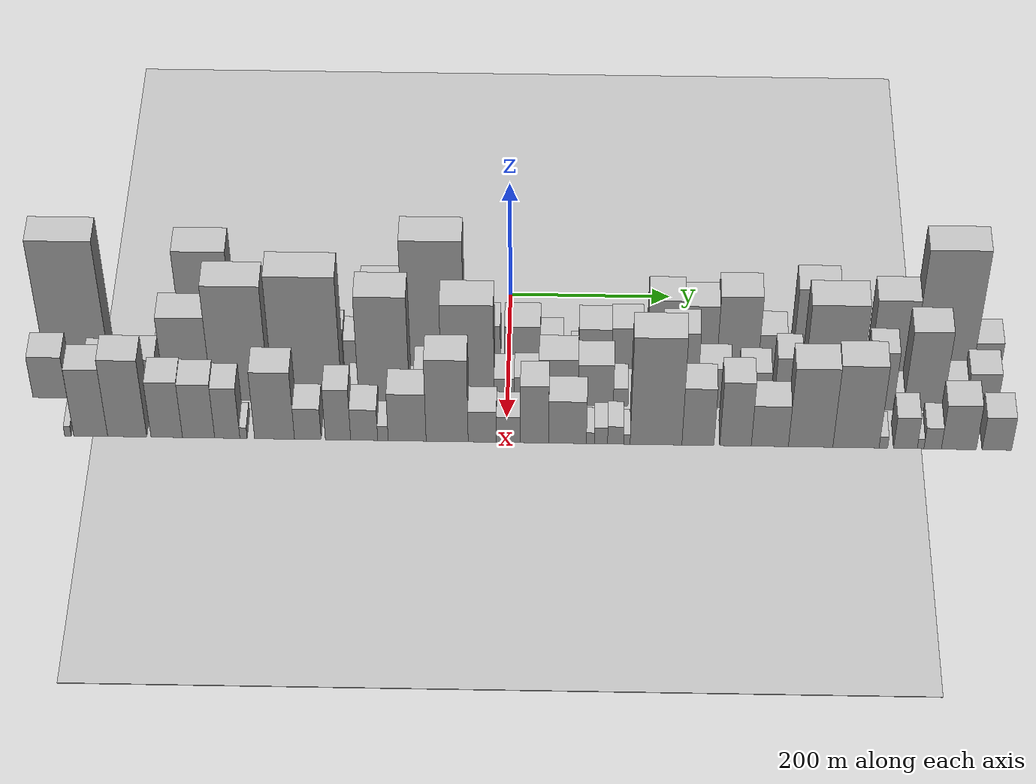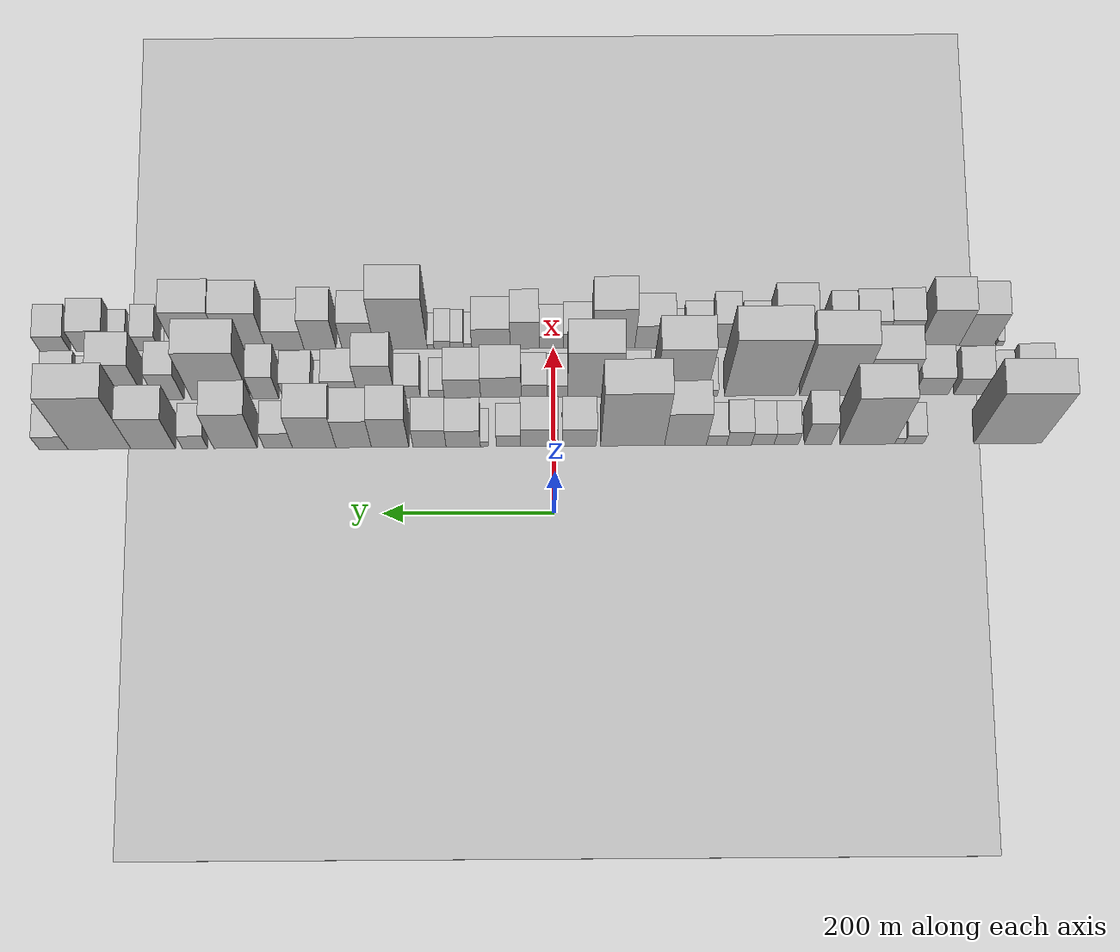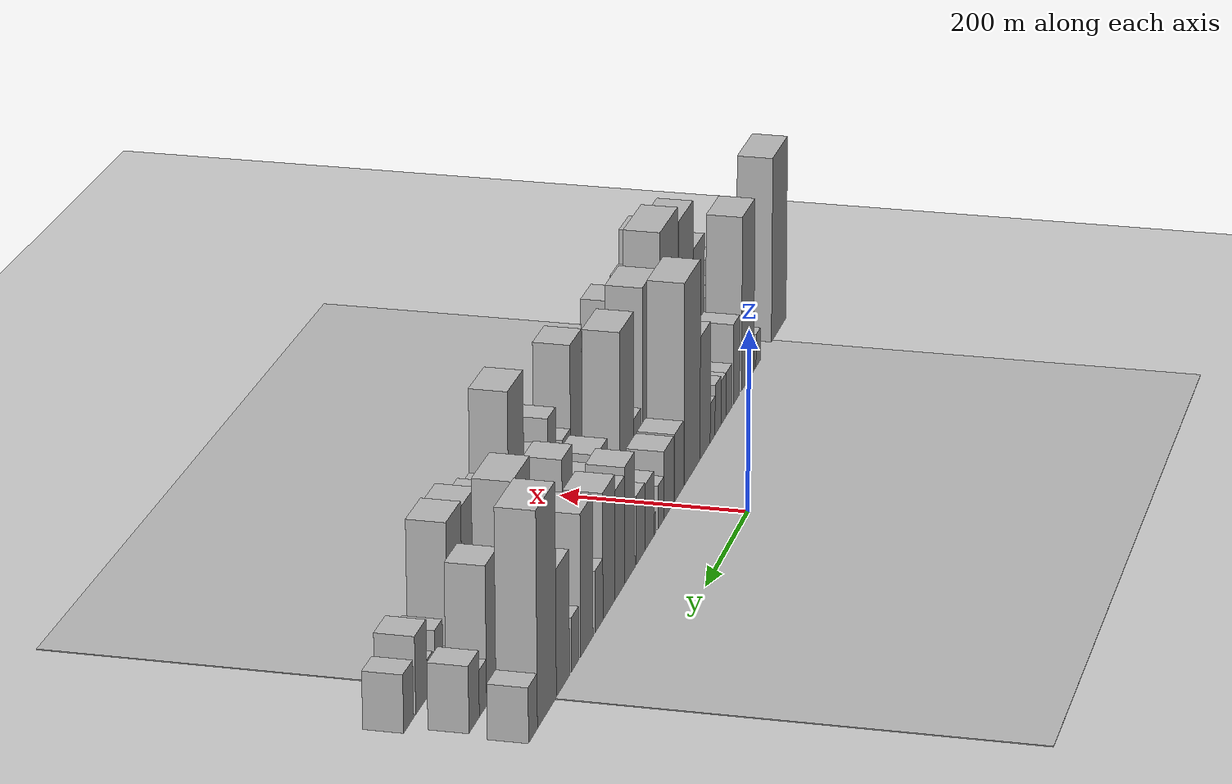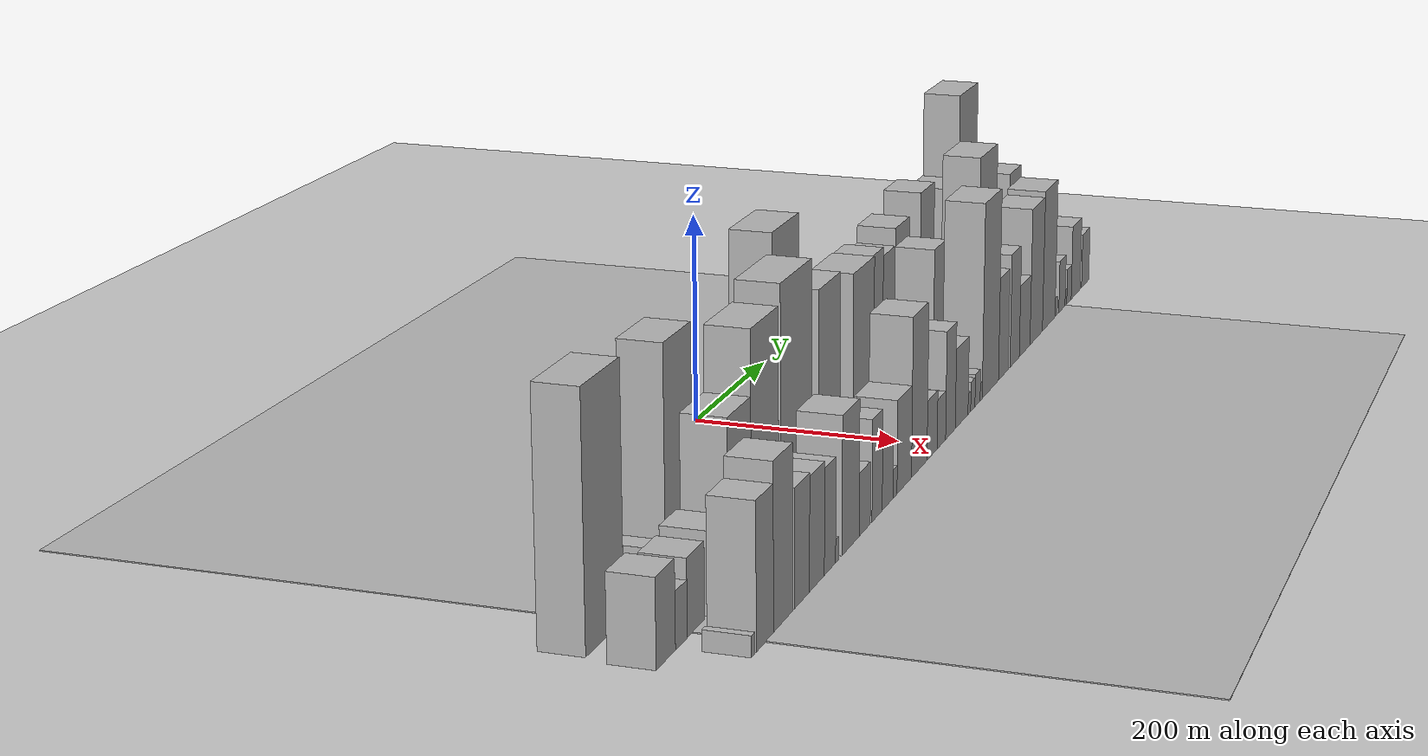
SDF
<?xml version="1.0" encoding="utf-8"?>

<sdf version="1.6">

   <world name="default">

      <gui fullscreen="0">

         <camera name="user_camera">

            <pose>-15 0 4.57585 0 0 0</pose>

            <view_controller>orbit</view_controller>

         </camera>

      </gui>

      <scene>

         <sky>

           <clouds>

             <speed>12</speed>

           </clouds>

         </sky>

         <ambient>0.4 0.4 0.4 1</ambient>

         <background>0.7 0.7 0.7 1</background>

         <shadows>1</shadows>

      </scene>

      <gravity>0 0 -9.8066</gravity>

      <magnetic_field>6e-06 2.3e-05 -4.2e-05</magnetic_field>

      <physics default="0" name="default_physics" type="ode">

         <ode>

            <solver>

               <type>quick</type>

               <iters>10</iters>

               <sor>1.0</sor>

               <use_dynamic_moi_rescaling>0</use_dynamic_moi_rescaling>

            </solver>

            <constraints>

               <cfm>0</cfm>

               <erp>0.2</erp>

               <contact_max_correcting_vel>100</contact_max_correcting_vel>

               <contact_surface_layer>0.001</contact_surface_layer>

            </constraints>

         </ode>

         <max_step_size>0.004</max_step_size>

         <real_time_factor>1</real_time_factor>

         <real_time_update_rate>250</real_time_update_rate>

      </physics>

      <light name="sun" type="directional">

         <cast_shadows>1</cast_shadows>

         <pose>0 0 10 0 0 0</pose>

         <diffuse>0.8 0.8 0.8 1</diffuse>

         <specular>0.2 0.2 0.2 1</specular>

         <attenuation>

            <range>1000</range>

            <constant>0.9</constant>

            <linear>0.01</linear>

            <quadratic>0.001</quadratic>

         </attenuation>

         <direction>-0.5 0.1 -0.9</direction>

      </light>

      <include>

         <name>ground_plane_1</name>

         <uri>model://HANNAS_ground_plane</uri>

         <pose>0 0 0  0 0 0</pose>

      </include>

      <include>

         <name>ground_plane_2</name>

         <uri>model://HANNAS_ground_plane</uri>

         <pose>100 0 0  0 0 0</pose>

      </include>

      <model name="building_1">

         <static>1</static>

         <pose frame="">100.0000 -533.1704 0 0.000000 0.000000 0.000000</pose>

         <link name="link">

            <pose frame="">0 0 108.00 0 0 0</pose>

            <collision name="collision">

               <geometry>

                  <box>

                     <size>40.0000 79.6592 216.0000</size>

                  </box>

               </geometry>

               <max_contacts>10</max_contacts>

               <surface>

                  <contact>

                     <ode/>

                  </contact>

                  <bounce/>

                  <friction>

                     <torsional>

                        <ode/>

                     </torsional>

                     <ode/>

                  </friction>

               </surface>

            </collision>

            <visual name="visual">

               <cast_shadows>0</cast_shadows>

               <geometry>

                  <box>

                     <size>40.0000 79.6592 216.0000</size>

                  </box>

               </geometry>

               <material>

                  <script>

                     <uri>model://HANNAS_wall/materials/scripts</uri>

                     <uri>model://HANNAS_wall/materials/textures</uri>

                     <name>vrc/HANNAS_wall</name>

                  </script>

               </material>

            </visual>

            <self_collide>0</self_collide>

            <enable_wind>0</enable_wind>

            <kinematic>0</kinematic>

         </link>

      </model>

      <model name="building_2">

         <static>1</static>

         <pose frame="">100.0000 -422.7327 0 0.000000 0.000000 0.000000</pose>

         <link name="link">

            <pose frame="">0 0 19.50 0 0 0</pose>

            <collision name="collision">

               <geometry>

                  <box>

                     <size>40.0000 22.4054 39.0000</size>

                  </box>

               </geometry>

               <max_contacts>10</max_contacts>

               <surface>

                  <contact>

                     <ode/>

                  </contact>

                  <bounce/>

                  <friction>

                     <torsional>

                        <ode/>

                     </torsional>

                     <ode/>

                  </friction>

               </surface>

            </collision>

            <visual name="visual">

               <cast_shadows>0</cast_shadows>

               <geometry>

                  <box>

                     <size>40.0000 22.4054 39.0000</size>

                  </box>

               </geometry>

               <material>

                  <script>

                     <uri>model://HANNAS_wall/materials/scripts</uri>

                     <uri>model://HANNAS_wall/materials/textures</uri>

                     <name>vrc/HANNAS_wall</name>

                  </script>

               </material>

            </visual>

            <self_collide>0</self_collide>

            <enable_wind>0</enable_wind>

            <kinematic>0</kinematic>

         </link>

      </model>

      <model name="building_3">

         <static>1</static>

         <pose frame="">100.0000 -405.9217 0 0.000000 0.000000 0.000000</pose>

         <link name="link">

            <pose frame="">0 0 13.50 0 0 0</pose>

            <collision name="collision">

               <geometry>

                  <box>

                     <size>40.0000 11.2166 27.0000</size>

                  </box>

               </geometry>

               <max_contacts>10</max_contacts>

               <surface>

                  <contact>

                     <ode/>

                  </contact>

                  <bounce/>

                  <friction>

                     <torsional>

                        <ode/>

                     </torsional>

                     <ode/>

                  </friction>

               </surface>

            </collision>

            <visual name="visual">

               <cast_shadows>0</cast_shadows>

               <geometry>

                  <box>

                     <size>40.0000 11.2166 27.0000</size>

                  </box>

               </geometry>

               <material>

                  <script>

                     <uri>model://HANNAS_wall/materials/scripts</uri>

                     <uri>model://HANNAS_wall/materials/textures</uri>

                     <name>vrc/HANNAS_wall</name>

                  </script>

               </material>

            </visual>

            <self_collide>0</self_collide>

            <enable_wind>0</enable_wind>

            <kinematic>0</kinematic>

         </link>

      </model>

      <model name="building_4">

         <static>1</static>

         <pose frame="">100.0000 -368.2056 0 0.000000 0.000000 0.000000</pose>

         <link name="link">

            <pose frame="">0 0 100.50 0 0 0</pose>

            <collision name="collision">

               <geometry>

                  <box>

                     <size>40.0000 64.2155 201.0000</size>

                  </box>

               </geometry>

               <max_contacts>10</max_contacts>

               <surface>

                  <contact>

                     <ode/>

                  </contact>

                  <bounce/>

                  <friction>

                     <torsional>

                        <ode/>

                     </torsional>

                     <ode/>

                  </friction>

               </surface>

            </collision>

            <visual name="visual">

               <cast_shadows>0</cast_shadows>

               <geometry>

                  <box>

                     <size>40.0000 64.2155 201.0000</size>

                  </box>

               </geometry>

               <material>

                  <script>

                     <uri>model://HANNAS_wall/materials/scripts</uri>

                     <uri>model://HANNAS_wall/materials/textures</uri>

                     <name>vrc/HANNAS_wall</name>

                  </script>

               </material>

            </visual>

            <self_collide>0</self_collide>

            <enable_wind>0</enable_wind>

            <kinematic>0</kinematic>

         </link>

      </model>

      <model name="building_5">

         <static>1</static>

         <pose frame="">100.0000 -310.0719 0 0.000000 0.000000 0.000000</pose>

         <link name="link">

            <pose frame="">0 0 46.50 0 0 0</pose>

            <collision name="collision">

               <geometry>

                  <box>

                     <size>40.0000 32.0519 93.0000</size>

                  </box>

               </geometry>

               <max_contacts>10</max_contacts>

               <surface>

                  <contact>

                     <ode/>

                  </contact>

                  <bounce/>

                  <friction>

                     <torsional>

                        <ode/>

                     </torsional>

                     <ode/>

                  </friction>

               </surface>

            </collision>

            <visual name="visual">

               <cast_shadows>0</cast_shadows>

               <geometry>

                  <box>

                     <size>40.0000 32.0519 93.0000</size>

                  </box>

               </geometry>

               <material>

                  <script>

                     <uri>model://HANNAS_wall/materials/scripts</uri>

                     <uri>model://HANNAS_wall/materials/textures</uri>

                     <name>vrc/HANNAS_wall</name>

                  </script>

               </material>

            </visual>

            <self_collide>0</self_collide>

            <enable_wind>0</enable_wind>

            <kinematic>0</kinematic>

         </link>

      </model>

      <model name="building_6">

         <static>1</static>

         <pose frame="">100.0000 -272.6769 0 0.000000 0.000000 0.000000</pose>

         <link name="link">

            <pose frame="">0 0 25.50 0 0 0</pose>

            <collision name="collision">

               <geometry>

                  <box>

                     <size>40.0000 28.7380 51.0000</size>

                  </box>

               </geometry>

               <max_contacts>10</max_contacts>

               <surface>

                  <contact>

                     <ode/>

                  </contact>

                  <bounce/>

                  <friction>

                     <torsional>

                        <ode/>

                     </torsional>

                     <ode/>

                  </friction>

               </surface>

            </collision>

            <visual name="visual">

               <cast_shadows>0</cast_shadows>

               <geometry>

                  <box>

                     <size>40.0000 28.7380 51.0000</size>

                  </box>

               </geometry>

               <material>

                  <script>

                     <uri>model://HANNAS_wall/materials/scripts</uri>

                     <uri>model://HANNAS_wall/materials/textures</uri>

                     <name>vrc/HANNAS_wall</name>

                  </script>

               </material>

            </visual>

            <self_collide>0</self_collide>

            <enable_wind>0</enable_wind>

            <kinematic>0</kinematic>

         </link>

      </model>

      <model name="building_7">

         <static>1</static>

         <pose frame="">100.0000 -245.1332 0 0.000000 0.000000 0.000000</pose>

         <link name="link">

            <pose frame="">0 0 25.50 0 0 0</pose>

            <collision name="collision">

               <geometry>

                  <box>

                     <size>40.0000 26.3495 51.0000</size>

                  </box>

               </geometry>

               <max_contacts>10</max_contacts>

               <surface>

                  <contact>

                     <ode/>

                  </contact>

                  <bounce/>

                  <friction>

                     <torsional>

                        <ode/>

                     </torsional>

                     <ode/>

                  </friction>

               </surface>

            </collision>

            <visual name="visual">

               <cast_shadows>0</cast_shadows>

               <geometry>

                  <box>

                     <size>40.0000 26.3495 51.0000</size>

                  </box>

               </geometry>

               <material>

                  <script>

                     <uri>model://HANNAS_wall/materials/scripts</uri>

                     <uri>model://HANNAS_wall/materials/textures</uri>

                     <name>vrc/HANNAS_wall</name>

                  </script>

               </material>

            </visual>

            <self_collide>0</self_collide>

            <enable_wind>0</enable_wind>

            <kinematic>0</kinematic>

         </link>

      </model>

      <model name="building_8">

         <static>1</static>

         <pose frame="">100.0000 -217.3423 0 0.000000 0.000000 0.000000</pose>

         <link name="link">

            <pose frame="">0 0 28.50 0 0 0</pose>

            <collision name="collision">

               <geometry>

                  <box>

                     <size>40.0000 29.2323 57.0000</size>

                  </box>

               </geometry>

               <max_contacts>10</max_contacts>

               <surface>

                  <contact>

                     <ode/>

                  </contact>

                  <bounce/>

                  <friction>

                     <torsional>

                        <ode/>

                     </torsional>

                     <ode/>

                  </friction>

               </surface>

            </collision>

            <visual name="visual">

               <cast_shadows>0</cast_shadows>

               <geometry>

                  <box>

                     <size>40.0000 29.2323 57.0000</size>

                  </box>

               </geometry>

               <material>

                  <script>

                     <uri>model://HANNAS_wall/materials/scripts</uri>

                     <uri>model://HANNAS_wall/materials/textures</uri>

                     <name>vrc/HANNAS_wall</name>

                  </script>

               </material>

            </visual>

            <self_collide>0</self_collide>

            <enable_wind>0</enable_wind>

            <kinematic>0</kinematic>

         </link>

      </model>

      <model name="building_9">

         <static>1</static>

         <pose frame="">100.0000 -190.7932 0 0.000000 0.000000 0.000000</pose>

         <link name="link">

            <pose frame="">0 0 22.50 0 0 0</pose>

            <collision name="collision">

               <geometry>

                  <box>

                     <size>40.0000 23.8659 45.0000</size>

                  </box>

               </geometry>

               <max_contacts>10</max_contacts>

               <surface>

                  <contact>

                     <ode/>

                  </contact>

                  <bounce/>

                  <friction>

                     <torsional>

                        <ode/>

                     </torsional>

                     <ode/>

                  </friction>

               </surface>

            </collision>

            <visual name="visual">

               <cast_shadows>0</cast_shadows>

               <geometry>

                  <box>

                     <size>40.0000 23.8659 45.0000</size>

                  </box>

               </geometry>

               <material>

                  <script>

                     <uri>model://HANNAS_wall/materials/scripts</uri>

                     <uri>model://HANNAS_wall/materials/textures</uri>

                     <name>vrc/HANNAS_wall</name>

                  </script>

               </material>

            </visual>

            <self_collide>0</self_collide>

            <enable_wind>0</enable_wind>

            <kinematic>0</kinematic>

         </link>

      </model>

      <model name="building_10">

         <static>1</static>

         <pose frame="">100.0000 -154.3311 0 0.000000 0.000000 0.000000</pose>

         <link name="link">

            <pose frame="">0 0 69.00 0 0 0</pose>

            <collision name="collision">

               <geometry>

                  <box>

                     <size>40.0000 49.0584 138.0000</size>

                  </box>

               </geometry>

               <max_contacts>10</max_contacts>

               <surface>

                  <contact>

                     <ode/>

                  </contact>

                  <bounce/>

                  <friction>

                     <torsional>

                        <ode/>

                     </torsional>

                     <ode/>

                  </friction>

               </surface>

            </collision>

            <visual name="visual">

               <cast_shadows>0</cast_shadows>

               <geometry>

                  <box>

                     <size>40.0000 49.0584 138.0000</size>

                  </box>

               </geometry>

               <material>

                  <script>

                     <uri>model://HANNAS_wall/materials/scripts</uri>

                     <uri>model://HANNAS_wall/materials/textures</uri>

                     <name>vrc/HANNAS_wall</name>

                  </script>

               </material>

            </visual>

            <self_collide>0</self_collide>

            <enable_wind>0</enable_wind>

            <kinematic>0</kinematic>

         </link>

      </model>

      <model name="building_11">

         <static>1</static>

         <pose frame="">100.0000 -92.2065 0 0.000000 0.000000 0.000000</pose>

         <link name="link">

            <pose frame="">0 0 112.50 0 0 0</pose>

            <collision name="collision">

               <geometry>

                  <box>

                     <size>40.0000 75.1906 225.0000</size>

                  </box>

               </geometry>

               <max_contacts>10</max_contacts>

               <surface>

                  <contact>

                     <ode/>

                  </contact>

                  <bounce/>

                  <friction>

                     <torsional>

                        <ode/>

                     </torsional>

                     <ode/>

                  </friction>

               </surface>

            </collision>

            <visual name="visual">

               <cast_shadows>0</cast_shadows>

               <geometry>

                  <box>

                     <size>40.0000 75.1906 225.0000</size>

                  </box>

               </geometry>

               <material>

                  <script>

                     <uri>model://HANNAS_wall/materials/scripts</uri>

                     <uri>model://HANNAS_wall/materials/textures</uri>

                     <name>vrc/HANNAS_wall</name>

                  </script>

               </material>

            </visual>

            <self_collide>0</self_collide>

            <enable_wind>0</enable_wind>

            <kinematic>0</kinematic>

         </link>

      </model>

      <model name="building_12">

         <static>1</static>

         <pose frame="">100.0000 -29.7188 0 0.000000 0.000000 0.000000</pose>

         <link name="link">

            <pose frame="">0 0 37.50 0 0 0</pose>

            <collision name="collision">

               <geometry>

                  <box>

                     <size>40.0000 39.7849 75.0000</size>

                  </box>

               </geometry>

               <max_contacts>10</max_contacts>

               <surface>

                  <contact>

                     <ode/>

                  </contact>

                  <bounce/>

                  <friction>

                     <torsional>

                        <ode/>

                     </torsional>

                     <ode/>

                  </friction>

               </surface>

            </collision>

            <visual name="visual">

               <cast_shadows>0</cast_shadows>

               <geometry>

                  <box>

                     <size>40.0000 39.7849 75.0000</size>

                  </box>

               </geometry>

               <material>

                  <script>

                     <uri>model://HANNAS_wall/materials/scripts</uri>

                     <uri>model://HANNAS_wall/materials/textures</uri>

                     <name>vrc/HANNAS_wall</name>

                  </script>

               </material>

            </visual>

            <self_collide>0</self_collide>

            <enable_wind>0</enable_wind>

            <kinematic>0</kinematic>

         </link>

      </model>

      <model name="building_13">

         <static>1</static>

         <pose frame="">100.0000 17.2359 0 0.000000 0.000000 0.000000</pose>

         <link name="link">

            <pose frame="">0 0 37.50 0 0 0</pose>

            <collision name="collision">

               <geometry>

                  <box>

                     <size>40.0000 44.1244 75.0000</size>

                  </box>

               </geometry>

               <max_contacts>10</max_contacts>

               <surface>

                  <contact>

                     <ode/>

                  </contact>

                  <bounce/>

                  <friction>

                     <torsional>

                        <ode/>

                     </torsional>

                     <ode/>

                  </friction>

               </surface>

            </collision>

            <visual name="visual">

               <cast_shadows>0</cast_shadows>

               <geometry>

                  <box>

                     <size>40.0000 44.1244 75.0000</size>

                  </box>

               </geometry>

               <material>

                  <script>

                     <uri>model://HANNAS_wall/materials/scripts</uri>

                     <uri>model://HANNAS_wall/materials/textures</uri>

                     <name>vrc/HANNAS_wall</name>

                  </script>

               </material>

            </visual>

            <self_collide>0</self_collide>

            <enable_wind>0</enable_wind>

            <kinematic>0</kinematic>

         </link>

      </model>

      <model name="building_14">

         <static>1</static>

         <pose frame="">100.0000 53.4781 0 0.000000 0.000000 0.000000</pose>

         <link name="link">

            <pose frame="">0 0 24.00 0 0 0</pose>

            <collision name="collision">

               <geometry>

                  <box>

                     <size>40.0000 28.3602 48.0000</size>

                  </box>

               </geometry>

               <max_contacts>10</max_contacts>

               <surface>

                  <contact>

                     <ode/>

                  </contact>

                  <bounce/>

                  <friction>

                     <torsional>

                        <ode/>

                     </torsional>

                     <ode/>

                  </friction>

               </surface>

            </collision>

            <visual name="visual">

               <cast_shadows>0</cast_shadows>

               <geometry>

                  <box>

                     <size>40.0000 28.3602 48.0000</size>

                  </box>

               </geometry>

               <material>

                  <script>

                     <uri>model://HANNAS_wall/materials/scripts</uri>

                     <uri>model://HANNAS_wall/materials/textures</uri>

                     <name>vrc/HANNAS_wall</name>

                  </script>

               </material>

            </visual>

            <self_collide>0</self_collide>

            <enable_wind>0</enable_wind>

            <kinematic>0</kinematic>

         </link>

      </model>

      <model name="building_15">

         <static>1</static>

         <pose frame="">100.0000 81.5761 0 0.000000 0.000000 0.000000</pose>

         <link name="link">

            <pose frame="">0 0 12.00 0 0 0</pose>

            <collision name="collision">

               <geometry>

                  <box>

                     <size>40.0000 9.8357 24.0000</size>

                  </box>

               </geometry>

               <max_contacts>10</max_contacts>

               <surface>

                  <contact>

                     <ode/>

                  </contact>

                  <bounce/>

                  <friction>

                     <torsional>

                        <ode/>

                     </torsional>

                     <ode/>

                  </friction>

               </surface>

            </collision>

            <visual name="visual">

               <cast_shadows>0</cast_shadows>

               <geometry>

                  <box>

                     <size>40.0000 9.8357 24.0000</size>

                  </box>

               </geometry>

               <material>

                  <script>

                     <uri>model://HANNAS_wall/materials/scripts</uri>

                     <uri>model://HANNAS_wall/materials/textures</uri>

                     <name>vrc/HANNAS_wall</name>

                  </script>

               </material>

            </visual>

            <self_collide>0</self_collide>

            <enable_wind>0</enable_wind>

            <kinematic>0</kinematic>

         </link>

      </model>

      <model name="building_16">

         <static>1</static>

         <pose frame="">100.0000 106.6366 0 0.000000 0.000000 0.000000</pose>

         <link name="link">

            <pose frame="">0 0 36.00 0 0 0</pose>

            <collision name="collision">

               <geometry>

                  <box>

                     <size>40.0000 40.2854 72.0000</size>

                  </box>

               </geometry>

               <max_contacts>10</max_contacts>

               <surface>

                  <contact>

                     <ode/>

                  </contact>

                  <bounce/>

                  <friction>

                     <torsional>

                        <ode/>

                     </torsional>

                     <ode/>

                  </friction>

               </surface>

            </collision>

            <visual name="visual">

               <cast_shadows>0</cast_shadows>

               <geometry>

                  <box>

                     <size>40.0000 40.2854 72.0000</size>

                  </box>

               </geometry>

               <material>

                  <script>

                     <uri>model://HANNAS_wall/materials/scripts</uri>

                     <uri>model://HANNAS_wall/materials/textures</uri>

                     <name>vrc/HANNAS_wall</name>

                  </script>

               </material>

            </visual>

            <self_collide>0</self_collide>

            <enable_wind>0</enable_wind>

            <kinematic>0</kinematic>

         </link>

      </model>

      <model name="building_17">

         <static>1</static>

         <pose frame="">100.0000 146.1305 0 0.000000 0.000000 0.000000</pose>

         <link name="link">

            <pose frame="">0 0 37.50 0 0 0</pose>

            <collision name="collision">

               <geometry>

                  <box>

                     <size>40.0000 38.7023 75.0000</size>

                  </box>

               </geometry>

               <max_contacts>10</max_contacts>

               <surface>

                  <contact>

                     <ode/>

                  </contact>

                  <bounce/>

                  <friction>

                     <torsional>

                        <ode/>

                     </torsional>

                     <ode/>

                  </friction>

               </surface>

            </collision>

            <visual name="visual">

               <cast_shadows>0</cast_shadows>

               <geometry>

                  <box>

                     <size>40.0000 38.7023 75.0000</size>

                  </box>

               </geometry>

               <material>

                  <script>

                     <uri>model://HANNAS_wall/materials/scripts</uri>

                     <uri>model://HANNAS_wall/materials/textures</uri>

                     <name>vrc/HANNAS_wall</name>

                  </script>

               </material>

            </visual>

            <self_collide>0</self_collide>

            <enable_wind>0</enable_wind>

            <kinematic>0</kinematic>

         </link>

      </model>

      <model name="building_18">

         <static>1</static>

         <pose frame="">100.0000 192.3931 0 0.000000 0.000000 0.000000</pose>

         <link name="link">

            <pose frame="">0 0 63.00 0 0 0</pose>

            <collision name="collision">

               <geometry>

                  <box>

                     <size>40.0000 43.8229 126.0000</size>

                  </box>

               </geometry>

               <max_contacts>10</max_contacts>

               <surface>

                  <contact>

                     <ode/>

                  </contact>

                  <bounce/>

                  <friction>

                     <torsional>

                        <ode/>

                     </torsional>

                     <ode/>

                  </friction>

               </surface>

            </collision>

            <visual name="visual">

               <cast_shadows>0</cast_shadows>

               <geometry>

                  <box>

                     <size>40.0000 43.8229 126.0000</size>

                  </box>

               </geometry>

               <material>

                  <script>

                     <uri>model://HANNAS_wall/materials/scripts</uri>

                     <uri>model://HANNAS_wall/materials/textures</uri>

                     <name>vrc/HANNAS_wall</name>

                  </script>

               </material>

            </visual>

            <self_collide>0</self_collide>

            <enable_wind>0</enable_wind>

            <kinematic>0</kinematic>

         </link>

      </model>

      <model name="building_19">

         <static>1</static>

         <pose frame="">100.0000 235.1371 0 0.000000 0.000000 0.000000</pose>

         <link name="link">

            <pose frame="">0 0 58.50 0 0 0</pose>

            <collision name="collision">

               <geometry>

                  <box>

                     <size>40.0000 41.6652 117.0000</size>

                  </box>

               </geometry>

               <max_contacts>10</max_contacts>

               <surface>

                  <contact>

                     <ode/>

                  </contact>

                  <bounce/>

                  <friction>

                     <torsional>

                        <ode/>

                     </torsional>

                     <ode/>

                  </friction>

               </surface>

            </collision>

            <visual name="visual">

               <cast_shadows>0</cast_shadows>

               <geometry>

                  <box>

                     <size>40.0000 41.6652 117.0000</size>

                  </box>

               </geometry>

               <material>

                  <script>

                     <uri>model://HANNAS_wall/materials/scripts</uri>

                     <uri>model://HANNAS_wall/materials/textures</uri>

                     <name>vrc/HANNAS_wall</name>

                  </script>

               </material>

            </visual>

            <self_collide>0</self_collide>

            <enable_wind>0</enable_wind>

            <kinematic>0</kinematic>

         </link>

      </model>

      <model name="building_20">

         <static>1</static>

         <pose frame="">100.0000 281.5150 0 0.000000 0.000000 0.000000</pose>

         <link name="link">

            <pose frame="">0 0 67.50 0 0 0</pose>

            <collision name="collision">

               <geometry>

                  <box>

                     <size>40.0000 51.0905 135.0000</size>

                  </box>

               </geometry>

               <max_contacts>10</max_contacts>

               <surface>

                  <contact>

                     <ode/>

                  </contact>

                  <bounce/>

                  <friction>

                     <torsional>

                        <ode/>

                     </torsional>

                     <ode/>

                  </friction>

               </surface>

            </collision>

            <visual name="visual">

               <cast_shadows>0</cast_shadows>

               <geometry>

                  <box>

                     <size>40.0000 51.0905 135.0000</size>

                  </box>

               </geometry>

               <material>

                  <script>

                     <uri>model://HANNAS_wall/materials/scripts</uri>

                     <uri>model://HANNAS_wall/materials/textures</uri>

                     <name>vrc/HANNAS_wall</name>

                  </script>

               </material>

            </visual>

            <self_collide>0</self_collide>

            <enable_wind>0</enable_wind>

            <kinematic>0</kinematic>

         </link>

      </model>

      <model name="building_21">

         <static>1</static>

         <pose frame="">100.0000 323.8223 0 0.000000 0.000000 0.000000</pose>

         <link name="link">

            <pose frame="">0 0 33.00 0 0 0</pose>

            <collision name="collision">

               <geometry>

                  <box>

                     <size>40.0000 33.5241 66.0000</size>

                  </box>

               </geometry>

               <max_contacts>10</max_contacts>

               <surface>

                  <contact>

                     <ode/>

                  </contact>

                  <bounce/>

                  <friction>

                     <torsional>

                        <ode/>

                     </torsional>

                     <ode/>

                  </friction>

               </surface>

            </collision>

            <visual name="visual">

               <cast_shadows>0</cast_shadows>

               <geometry>

                  <box>

                     <size>40.0000 33.5241 66.0000</size>

                  </box>

               </geometry>

               <material>

                  <script>

                     <uri>model://HANNAS_wall/materials/scripts</uri>

                     <uri>model://HANNAS_wall/materials/textures</uri>

                     <name>vrc/HANNAS_wall</name>

                  </script>

               </material>

            </visual>

            <self_collide>0</self_collide>

            <enable_wind>0</enable_wind>

            <kinematic>0</kinematic>

         </link>

      </model>

      <model name="building_22">

         <static>1</static>

         <pose frame="">100.0000 374.0789 0 0.000000 0.000000 0.000000</pose>

         <link name="link">

            <pose frame="">0 0 75.00 0 0 0</pose>

            <collision name="collision">

               <geometry>

                  <box>

                     <size>40.0000 50.9891 150.0000</size>

                  </box>

               </geometry>

               <max_contacts>10</max_contacts>

               <surface>

                  <contact>

                     <ode/>

                  </contact>

                  <bounce/>

                  <friction>

                     <torsional>

                        <ode/>

                     </torsional>

                     <ode/>

                  </friction>

               </surface>

            </collision>

            <visual name="visual">

               <cast_shadows>0</cast_shadows>

               <geometry>

                  <box>

                     <size>40.0000 50.9891 150.0000</size>

                  </box>

               </geometry>

               <material>

                  <script>

                     <uri>model://HANNAS_wall/materials/scripts</uri>

                     <uri>model://HANNAS_wall/materials/textures</uri>

                     <name>vrc/HANNAS_wall</name>

                  </script>

               </material>

            </visual>

            <self_collide>0</self_collide>

            <enable_wind>0</enable_wind>

            <kinematic>0</kinematic>

         </link>

      </model>

      <model name="building_23">

         <static>1</static>

         <pose frame="">100.0000 421.5128 0 0.000000 0.000000 0.000000</pose>

         <link name="link">

            <pose frame="">0 0 28.50 0 0 0</pose>

            <collision name="collision">

               <geometry>

                  <box>

                     <size>40.0000 29.8788 57.0000</size>

                  </box>

               </geometry>

               <max_contacts>10</max_contacts>

               <surface>

                  <contact>

                     <ode/>

                  </contact>

                  <bounce/>

                  <friction>

                     <torsional>

                        <ode/>

                     </torsional>

                     <ode/>

                  </friction>

               </surface>

            </collision>

            <visual name="visual">

               <cast_shadows>0</cast_shadows>

               <geometry>

                  <box>

                     <size>40.0000 29.8788 57.0000</size>

                  </box>

               </geometry>

               <material>

                  <script>

                     <uri>model://HANNAS_wall/materials/scripts</uri>

                     <uri>model://HANNAS_wall/materials/textures</uri>

                     <name>vrc/HANNAS_wall</name>

                  </script>

               </material>

            </visual>

            <self_collide>0</self_collide>

            <enable_wind>0</enable_wind>

            <kinematic>0</kinematic>

         </link>

      </model>

      <model name="building_24">

         <static>1</static>

         <pose frame="">100.0000 470.6569 0 0.000000 0.000000 0.000000</pose>

         <link name="link">

            <pose frame="">0 0 66.00 0 0 0</pose>

            <collision name="collision">

               <geometry>

                  <box>

                     <size>40.0000 52.4093 132.0000</size>

                  </box>

               </geometry>

               <max_contacts>10</max_contacts>

               <surface>

                  <contact>

                     <ode/>

                  </contact>

                  <bounce/>

                  <friction>

                     <torsional>

                        <ode/>

                     </torsional>

                     <ode/>

                  </friction>

               </surface>

            </collision>

            <visual name="visual">

               <cast_shadows>0</cast_shadows>

               <geometry>

                  <box>

                     <size>40.0000 52.4093 132.0000</size>

                  </box>

               </geometry>

               <material>

                  <script>

                     <uri>model://HANNAS_wall/materials/scripts</uri>

                     <uri>model://HANNAS_wall/materials/textures</uri>

                     <name>vrc/HANNAS_wall</name>

                  </script>

               </material>

            </visual>

            <self_collide>0</self_collide>

            <enable_wind>0</enable_wind>

            <kinematic>0</kinematic>

         </link>

      </model>

      <model name="building_25">

         <static>1</static>

         <pose frame="">100.0000 533.7345 0 0.000000 0.000000 0.000000</pose>

         <link name="link">

            <pose frame="">0 0 111.00 0 0 0</pose>

            <collision name="collision">

               <geometry>

                  <box>

                     <size>40.0000 73.7459 222.0000</size>

                  </box>

               </geometry>

               <max_contacts>10</max_contacts>

               <surface>

                  <contact>

                     <ode/>

                  </contact>

                  <bounce/>

                  <friction>

                     <torsional>

                        <ode/>

                     </torsional>

                     <ode/>

                  </friction>

               </surface>

            </collision>

            <visual name="visual">

               <cast_shadows>0</cast_shadows>

               <geometry>

                  <box>

                     <size>40.0000 73.7459 222.0000</size>

                  </box>

               </geometry>

               <material>

                  <script>

                     <uri>model://HANNAS_wall/materials/scripts</uri>

                     <uri>model://HANNAS_wall/materials/textures</uri>

                     <name>vrc/HANNAS_wall</name>

                  </script>

               </material>

            </visual>

            <self_collide>0</self_collide>

            <enable_wind>0</enable_wind>

            <kinematic>0</kinematic>

         </link>

      </model>

      <model name="building_26">

         <static>1</static>

         <pose frame="">100.0000 587.5688 0 0.000000 0.000000 0.000000</pose>

         <link name="link">

            <pose frame="">0 0 28.50 0 0 0</pose>

            <collision name="collision">

               <geometry>

                  <box>

                     <size>40.0000 33.9228 57.0000</size>

                  </box>

               </geometry>

               <max_contacts>10</max_contacts>

               <surface>

                  <contact>

                     <ode/>

                  </contact>

                  <bounce/>

                  <friction>

                     <torsional>

                        <ode/>

                     </torsional>

                     <ode/>

                  </friction>

               </surface>

            </collision>

            <visual name="visual">

               <cast_shadows>0</cast_shadows>

               <geometry>

                  <box>

                     <size>40.0000 33.9228 57.0000</size>

                  </box>

               </geometry>

               <material>

                  <script>

                     <uri>model://HANNAS_wall/materials/scripts</uri>

                     <uri>model://HANNAS_wall/materials/textures</uri>

                     <name>vrc/HANNAS_wall</name>

                  </script>

               </material>

            </visual>

            <self_collide>0</self_collide>

            <enable_wind>0</enable_wind>

            <kinematic>0</kinematic>

         </link>

      </model>

      <model name="building_27">

         <static>1</static>

         <pose frame="">160.0000 -559.2378 0 0.000000 0.000000 0.000000</pose>

         <link name="link">

            <pose frame="">0 0 37.50 0 0 0</pose>

            <collision name="collision">

               <geometry>

                  <box>

                     <size>40.0000 41.5244 75.0000</size>

                  </box>

               </geometry>

               <max_contacts>10</max_contacts>

               <surface>

                  <contact>

                     <ode/>

                  </contact>

                  <bounce/>

                  <friction>

                     <torsional>

                        <ode/>

                     </torsional>

                     <ode/>

                  </friction>

               </surface>

            </collision>

            <visual name="visual">

               <cast_shadows>0</cast_shadows>

               <geometry>

                  <box>

                     <size>40.0000 41.5244 75.0000</size>

                  </box>

               </geometry>

               <material>

                  <script>

                     <uri>model://HANNAS_wall/materials/scripts</uri>

                     <uri>model://HANNAS_wall/materials/textures</uri>

                     <name>vrc/HANNAS_wall</name>

                  </script>

               </material>

            </visual>

            <self_collide>0</self_collide>

            <enable_wind>0</enable_wind>

            <kinematic>0</kinematic>

         </link>

      </model>

      <model name="building_28">

         <static>1</static>

         <pose frame="">160.0000 -525.4002 0 0.000000 0.000000 0.000000</pose>

         <link name="link">

            <pose frame="">0 0 24.00 0 0 0</pose>

            <collision name="collision">

               <geometry>

                  <box>

                     <size>40.0000 26.1507 48.0000</size>

                  </box>

               </geometry>

               <max_contacts>10</max_contacts>

               <surface>

                  <contact>

                     <ode/>

                  </contact>

                  <bounce/>

                  <friction>

                     <torsional>

                        <ode/>

                     </torsional>

                     <ode/>

                  </friction>

               </surface>

            </collision>

            <visual name="visual">

               <cast_shadows>0</cast_shadows>

               <geometry>

                  <box>

                     <size>40.0000 26.1507 48.0000</size>

                  </box>

               </geometry>

               <material>

                  <script>

                     <uri>model://HANNAS_wall/materials/scripts</uri>

                     <uri>model://HANNAS_wall/materials/textures</uri>

                     <name>vrc/HANNAS_wall</name>

                  </script>

               </material>

            </visual>

            <self_collide>0</self_collide>

            <enable_wind>0</enable_wind>

            <kinematic>0</kinematic>

         </link>

      </model>

      <model name="building_29">

         <static>1</static>

         <pose frame="">160.0000 -492.6658 0 0.000000 0.000000 0.000000</pose>

         <link name="link">

            <pose frame="">0 0 33.00 0 0 0</pose>

            <collision name="collision">

               <geometry>

                  <box>

                     <size>40.0000 39.3182 66.0000</size>

                  </box>

               </geometry>

               <max_contacts>10</max_contacts>

               <surface>

                  <contact>

                     <ode/>

                  </contact>

                  <bounce/>

                  <friction>

                     <torsional>

                        <ode/>

                     </torsional>

                     <ode/>

                  </friction>

               </surface>

            </collision>

            <visual name="visual">

               <cast_shadows>0</cast_shadows>

               <geometry>

                  <box>

                     <size>40.0000 39.3182 66.0000</size>

                  </box>

               </geometry>

               <material>

                  <script>

                     <uri>model://HANNAS_wall/materials/scripts</uri>

                     <uri>model://HANNAS_wall/materials/textures</uri>

                     <name>vrc/HANNAS_wall</name>

                  </script>

               </material>

            </visual>

            <self_collide>0</self_collide>

            <enable_wind>0</enable_wind>

            <kinematic>0</kinematic>

         </link>

      </model>

      <model name="building_30">

         <static>1</static>

         <pose frame="">160.0000 -445.9524 0 0.000000 0.000000 0.000000</pose>

         <link name="link">

            <pose frame="">0 0 36.00 0 0 0</pose>

            <collision name="collision">

               <geometry>

                  <box>

                     <size>40.0000 40.1085 72.0000</size>

                  </box>

               </geometry>

               <max_contacts>10</max_contacts>

               <surface>

                  <contact>

                     <ode/>

                  </contact>

                  <bounce/>

                  <friction>

                     <torsional>

                        <ode/>

                     </torsional>

                     <ode/>

                  </friction>

               </surface>

            </collision>

            <visual name="visual">

               <cast_shadows>0</cast_shadows>

               <geometry>

                  <box>

                     <size>40.0000 40.1085 72.0000</size>

                  </box>

               </geometry>

               <material>

                  <script>

                     <uri>model://HANNAS_wall/materials/scripts</uri>

                     <uri>model://HANNAS_wall/materials/textures</uri>

                     <name>vrc/HANNAS_wall</name>

                  </script>

               </material>

            </visual>

            <self_collide>0</self_collide>

            <enable_wind>0</enable_wind>

            <kinematic>0</kinematic>

         </link>

      </model>

      <model name="building_31">

         <static>1</static>

         <pose frame="">160.0000 -389.2653 0 0.000000 0.000000 0.000000</pose>

         <link name="link">

            <pose frame="">0 0 75.00 0 0 0</pose>

            <collision name="collision">

               <geometry>

                  <box>

                     <size>40.0000 57.2656 150.0000</size>

                  </box>

               </geometry>

               <max_contacts>10</max_contacts>

               <surface>

                  <contact>

                     <ode/>

                  </contact>

                  <bounce/>

                  <friction>

                     <torsional>

                        <ode/>

                     </torsional>

                     <ode/>

                  </friction>

               </surface>

            </collision>

            <visual name="visual">

               <cast_shadows>0</cast_shadows>

               <geometry>

                  <box>

                     <size>40.0000 57.2656 150.0000</size>

                  </box>

               </geometry>

               <material>

                  <script>

                     <uri>model://HANNAS_wall/materials/scripts</uri>

                     <uri>model://HANNAS_wall/materials/textures</uri>

                     <name>vrc/HANNAS_wall</name>

                  </script>

               </material>

            </visual>

            <self_collide>0</self_collide>

            <enable_wind>0</enable_wind>

            <kinematic>0</kinematic>

         </link>

      </model>

      <model name="building_32">

         <static>1</static>

         <pose frame="">160.0000 -325.5553 0 0.000000 0.000000 0.000000</pose>

         <link name="link">

            <pose frame="">0 0 103.50 0 0 0</pose>

            <collision name="collision">

               <geometry>

                  <box>

                     <size>40.0000 70.1543 207.0000</size>

                  </box>

               </geometry>

               <max_contacts>10</max_contacts>

               <surface>

                  <contact>

                     <ode/>

                  </contact>

                  <bounce/>

                  <friction>

                     <torsional>

                        <ode/>

                     </torsional>

                     <ode/>

                  </friction>

               </surface>

            </collision>

            <visual name="visual">

               <cast_shadows>0</cast_shadows>

               <geometry>

                  <box>

                     <size>40.0000 70.1543 207.0000</size>

                  </box>

               </geometry>

               <material>

                  <script>

                     <uri>model://HANNAS_wall/materials/scripts</uri>

                     <uri>model://HANNAS_wall/materials/textures</uri>

                     <name>vrc/HANNAS_wall</name>

                  </script>

               </material>

            </visual>

            <self_collide>0</self_collide>

            <enable_wind>0</enable_wind>

            <kinematic>0</kinematic>

         </link>

      </model>

      <model name="building_33">

         <static>1</static>

         <pose frame="">160.0000 -243.4964 0 0.000000 0.000000 0.000000</pose>

         <link name="link">

            <pose frame="">0 0 112.50 0 0 0</pose>

            <collision name="collision">

               <geometry>

                  <box>

                     <size>40.0000 83.9636 225.0000</size>

                  </box>

               </geometry>

               <max_contacts>10</max_contacts>

               <surface>

                  <contact>

                     <ode/>

                  </contact>

                  <bounce/>

                  <friction>

                     <torsional>

                        <ode/>

                     </torsional>

                     <ode/>

                  </friction>

               </surface>

            </collision>

            <visual name="visual">

               <cast_shadows>0</cast_shadows>

               <geometry>

                  <box>

                     <size>40.0000 83.9636 225.0000</size>

                  </box>

               </geometry>

               <material>

                  <script>

                     <uri>model://HANNAS_wall/materials/scripts</uri>

                     <uri>model://HANNAS_wall/materials/textures</uri>

                     <name>vrc/HANNAS_wall</name>

                  </script>

               </material>

            </visual>

            <self_collide>0</self_collide>

            <enable_wind>0</enable_wind>

            <kinematic>0</kinematic>

         </link>

      </model>

      <model name="building_34">

         <static>1</static>

         <pose frame="">160.0000 -187.3858 0 0.000000 0.000000 0.000000</pose>

         <link name="link">

            <pose frame="">0 0 13.50 0 0 0</pose>

            <collision name="collision">

               <geometry>

                  <box>

                     <size>40.0000 12.2575 27.0000</size>

                  </box>

               </geometry>

               <max_contacts>10</max_contacts>

               <surface>

                  <contact>

                     <ode/>

                  </contact>

                  <bounce/>

                  <friction>

                     <torsional>

                        <ode/>

                     </torsional>

                     <ode/>

                  </friction>

               </surface>

            </collision>

            <visual name="visual">

               <cast_shadows>0</cast_shadows>

               <geometry>

                  <box>

                     <size>40.0000 12.2575 27.0000</size>

                  </box>

               </geometry>

               <material>

                  <script>

                     <uri>model://HANNAS_wall/materials/scripts</uri>

                     <uri>model://HANNAS_wall/materials/textures</uri>

                     <name>vrc/HANNAS_wall</name>

                  </script>

               </material>

            </visual>

            <self_collide>0</self_collide>

            <enable_wind>0</enable_wind>

            <kinematic>0</kinematic>

         </link>

      </model>

      <model name="building_35">

         <static>1</static>

         <pose frame="">160.0000 -150.2522 0 0.000000 0.000000 0.000000</pose>

         <link name="link">

            <pose frame="">0 0 96.00 0 0 0</pose>

            <collision name="collision">

               <geometry>

                  <box>

                     <size>40.0000 62.0097 192.0000</size>

                  </box>

               </geometry>

               <max_contacts>10</max_contacts>

               <surface>

                  <contact>

                     <ode/>

                  </contact>

                  <bounce/>

                  <friction>

                     <torsional>

                        <ode/>

                     </torsional>

                     <ode/>

                  </friction>

               </surface>

            </collision>

            <visual name="visual">

               <cast_shadows>0</cast_shadows>

               <geometry>

                  <box>

                     <size>40.0000 62.0097 192.0000</size>

                  </box>

               </geometry>

               <material>

                  <script>

                     <uri>model://HANNAS_wall/materials/scripts</uri>

                     <uri>model://HANNAS_wall/materials/textures</uri>

                     <name>vrc/HANNAS_wall</name>

                  </script>

               </material>

            </visual>

            <self_collide>0</self_collide>

            <enable_wind>0</enable_wind>

            <kinematic>0</kinematic>

         </link>

      </model>

      <model name="building_36">

         <static>1</static>

         <pose frame="">160.0000 -96.7051 0 0.000000 0.000000 0.000000</pose>

         <link name="link">

            <pose frame="">0 0 30.00 0 0 0</pose>

            <collision name="collision">

               <geometry>

                  <box>

                     <size>40.0000 33.0845 60.0000</size>

                  </box>

               </geometry>

               <max_contacts>10</max_contacts>

               <surface>

                  <contact>

                     <ode/>

                  </contact>

                  <bounce/>

                  <friction>

                     <torsional>

                        <ode/>

                     </torsional>

                     <ode/>

                  </friction>

               </surface>

            </collision>

            <visual name="visual">

               <cast_shadows>0</cast_shadows>

               <geometry>

                  <box>

                     <size>40.0000 33.0845 60.0000</size>

                  </box>

               </geometry>

               <material>

                  <script>

                     <uri>model://HANNAS_wall/materials/scripts</uri>

                     <uri>model://HANNAS_wall/materials/textures</uri>

                     <name>vrc/HANNAS_wall</name>

                  </script>

               </material>

            </visual>

            <self_collide>0</self_collide>

            <enable_wind>0</enable_wind>

            <kinematic>0</kinematic>

         </link>

      </model>

      <model name="building_37">

         <static>1</static>

         <pose frame="">160.0000 -48.1493 0 0.000000 0.000000 0.000000</pose>

         <link name="link">

            <pose frame="">0 0 90.00 0 0 0</pose>

            <collision name="collision">

               <geometry>

                  <box>

                     <size>40.0000 64.0271 180.0000</size>

                  </box>

               </geometry>

               <max_contacts>10</max_contacts>

               <surface>

                  <contact>

                     <ode/>

                  </contact>

                  <bounce/>

                  <friction>

                     <torsional>

                        <ode/>

                     </torsional>

                     <ode/>

                  </friction>

               </surface>

            </collision>

            <visual name="visual">

               <cast_shadows>0</cast_shadows>

               <geometry>

                  <box>

                     <size>40.0000 64.0271 180.0000</size>

                  </box>

               </geometry>

               <material>

                  <script>

                     <uri>model://HANNAS_wall/materials/scripts</uri>

                     <uri>model://HANNAS_wall/materials/textures</uri>

                     <name>vrc/HANNAS_wall</name>

                  </script>

               </material>

            </visual>

            <self_collide>0</self_collide>

            <enable_wind>0</enable_wind>

            <kinematic>0</kinematic>

         </link>

      </model>

      <model name="building_38">

         <static>1</static>

         <pose frame="">160.0000 -3.9642 0 0.000000 0.000000 0.000000</pose>

         <link name="link">

            <pose frame="">0 0 24.00 0 0 0</pose>

            <collision name="collision">

               <geometry>

                  <box>

                     <size>40.0000 24.3431 48.0000</size>

                  </box>

               </geometry>

               <max_contacts>10</max_contacts>

               <surface>

                  <contact>

                     <ode/>

                  </contact>

                  <bounce/>

                  <friction>

                     <torsional>

                        <ode/>

                     </torsional>

                     <ode/>

                  </friction>

               </surface>

            </collision>

            <visual name="visual">

               <cast_shadows>0</cast_shadows>

               <geometry>

                  <box>

                     <size>40.0000 24.3431 48.0000</size>

                  </box>

               </geometry>

               <material>

                  <script>

                     <uri>model://HANNAS_wall/materials/scripts</uri>

                     <uri>model://HANNAS_wall/materials/textures</uri>

                     <name>vrc/HANNAS_wall</name>

                  </script>

               </material>

            </visual>

            <self_collide>0</self_collide>

            <enable_wind>0</enable_wind>

            <kinematic>0</kinematic>

         </link>

      </model>

      <model name="building_39">

         <static>1</static>

         <pose frame="">160.0000 23.2347 0 0.000000 0.000000 0.000000</pose>

         <link name="link">

            <pose frame="">0 0 25.50 0 0 0</pose>

            <collision name="collision">

               <geometry>

                  <box>

                     <size>40.0000 30.0547 51.0000</size>

                  </box>

               </geometry>

               <max_contacts>10</max_contacts>

               <surface>

                  <contact>

                     <ode/>

                  </contact>

                  <bounce/>

                  <friction>

                     <torsional>

                        <ode/>

                     </torsional>

                     <ode/>

                  </friction>

               </surface>

            </collision>

            <visual name="visual">

               <cast_shadows>0</cast_shadows>

               <geometry>

                  <box>

                     <size>40.0000 30.0547 51.0000</size>

                  </box>

               </geometry>

               <material>

                  <script>

                     <uri>model://HANNAS_wall/materials/scripts</uri>

                     <uri>model://HANNAS_wall/materials/textures</uri>

                     <name>vrc/HANNAS_wall</name>

                  </script>

               </material>

            </visual>

            <self_collide>0</self_collide>

            <enable_wind>0</enable_wind>

            <kinematic>0</kinematic>

         </link>

      </model>

      <model name="building_40">

         <static>1</static>

         <pose frame="">160.0000 62.1663 0 0.000000 0.000000 0.000000</pose>

         <link name="link">

            <pose frame="">0 0 42.00 0 0 0</pose>

            <collision name="collision">

               <geometry>

                  <box>

                     <size>40.0000 47.8087 84.0000</size>

                  </box>

               </geometry>

               <max_contacts>10</max_contacts>

               <surface>

                  <contact>

                     <ode/>

                  </contact>

                  <bounce/>

                  <friction>

                     <torsional>

                        <ode/>

                     </torsional>

                     <ode/>

                  </friction>

               </surface>

            </collision>

            <visual name="visual">

               <cast_shadows>0</cast_shadows>

               <geometry>

                  <box>

                     <size>40.0000 47.8087 84.0000</size>

                  </box>

               </geometry>

               <material>

                  <script>

                     <uri>model://HANNAS_wall/materials/scripts</uri>

                     <uri>model://HANNAS_wall/materials/textures</uri>

                     <name>vrc/HANNAS_wall</name>

                  </script>

               </material>

            </visual>

            <self_collide>0</self_collide>

            <enable_wind>0</enable_wind>

            <kinematic>0</kinematic>

         </link>

      </model>

      <model name="building_41">

         <static>1</static>

         <pose frame="">160.0000 107.5418 0 0.000000 0.000000 0.000000</pose>

         <link name="link">

            <pose frame="">0 0 37.50 0 0 0</pose>

            <collision name="collision">

               <geometry>

                  <box>

                     <size>40.0000 42.9423 75.0000</size>

                  </box>

               </geometry>

               <max_contacts>10</max_contacts>

               <surface>

                  <contact>

                     <ode/>

                  </contact>

                  <bounce/>

                  <friction>

                     <torsional>

                        <ode/>

                     </torsional>

                     <ode/>

                  </friction>

               </surface>

            </collision>

            <visual name="visual">

               <cast_shadows>0</cast_shadows>

               <geometry>

                  <box>

                     <size>40.0000 42.9423 75.0000</size>

                  </box>

               </geometry>

               <material>

                  <script>

                     <uri>model://HANNAS_wall/materials/scripts</uri>

                     <uri>model://HANNAS_wall/materials/textures</uri>

                     <name>vrc/HANNAS_wall</name>

                  </script>

               </material>

            </visual>

            <self_collide>0</self_collide>

            <enable_wind>0</enable_wind>

            <kinematic>0</kinematic>

         </link>

      </model>

      <model name="building_42">

         <static>1</static>

         <pose frame="">160.0000 138.0352 0 0.000000 0.000000 0.000000</pose>

         <link name="link">

            <pose frame="">0 0 16.50 0 0 0</pose>

            <collision name="collision">

               <geometry>

                  <box>

                     <size>40.0000 18.0444 33.0000</size>

                  </box>

               </geometry>

               <max_contacts>10</max_contacts>

               <surface>

                  <contact>

                     <ode/>

                  </contact>

                  <bounce/>

                  <friction>

                     <torsional>

                        <ode/>

                     </torsional>

                     <ode/>

                  </friction>

               </surface>

            </collision>

            <visual name="visual">

               <cast_shadows>0</cast_shadows>

               <geometry>

                  <box>

                     <size>40.0000 18.0444 33.0000</size>

                  </box>

               </geometry>

               <material>

                  <script>

                     <uri>model://HANNAS_wall/materials/scripts</uri>

                     <uri>model://HANNAS_wall/materials/textures</uri>

                     <name>vrc/HANNAS_wall</name>

                  </script>

               </material>

            </visual>

            <self_collide>0</self_collide>

            <enable_wind>0</enable_wind>

            <kinematic>0</kinematic>

         </link>

      </model>

      <model name="building_43">

         <static>1</static>

         <pose frame="">160.0000 171.9871 0 0.000000 0.000000 0.000000</pose>

         <link name="link">

            <pose frame="">0 0 25.50 0 0 0</pose>

            <collision name="collision">

               <geometry>

                  <box>

                     <size>40.0000 29.8594 51.0000</size>

                  </box>

               </geometry>

               <max_contacts>10</max_contacts>

               <surface>

                  <contact>

                     <ode/>

                  </contact>

                  <bounce/>

                  <friction>

                     <torsional>

                        <ode/>

                     </torsional>

                     <ode/>

                  </friction>

               </surface>

            </collision>

            <visual name="visual">

               <cast_shadows>0</cast_shadows>

               <geometry>

                  <box>

                     <size>40.0000 29.8594 51.0000</size>

                  </box>

               </geometry>

               <material>

                  <script>

                     <uri>model://HANNAS_wall/materials/scripts</uri>

                     <uri>model://HANNAS_wall/materials/textures</uri>

                     <name>vrc/HANNAS_wall</name>

                  </script>

               </material>

            </visual>

            <self_collide>0</self_collide>

            <enable_wind>0</enable_wind>

            <kinematic>0</kinematic>

         </link>

      </model>

      <model name="building_44">

         <static>1</static>

         <pose frame="">160.0000 208.7328 0 0.000000 0.000000 0.000000</pose>

         <link name="link">

            <pose frame="">0 0 67.50 0 0 0</pose>

            <collision name="collision">

               <geometry>

                  <box>

                     <size>40.0000 43.6321 135.0000</size>

                  </box>

               </geometry>

               <max_contacts>10</max_contacts>

               <surface>

                  <contact>

                     <ode/>

                  </contact>

                  <bounce/>

                  <friction>

                     <torsional>

                        <ode/>

                     </torsional>

                     <ode/>

                  </friction>

               </surface>

            </collision>

            <visual name="visual">

               <cast_shadows>0</cast_shadows>

               <geometry>

                  <box>

                     <size>40.0000 43.6321 135.0000</size>

                  </box>

               </geometry>

               <material>

                  <script>

                     <uri>model://HANNAS_wall/materials/scripts</uri>

                     <uri>model://HANNAS_wall/materials/textures</uri>

                     <name>vrc/HANNAS_wall</name>

                  </script>

               </material>

            </visual>

            <self_collide>0</self_collide>

            <enable_wind>0</enable_wind>

            <kinematic>0</kinematic>

         </link>

      </model>

      <model name="building_45">

         <static>1</static>

         <pose frame="">160.0000 250.6235 0 0.000000 0.000000 0.000000</pose>

         <link name="link">

            <pose frame="">0 0 36.00 0 0 0</pose>

            <collision name="collision">

               <geometry>

                  <box>

                     <size>40.0000 40.1493 72.0000</size>

                  </box>

               </geometry>

               <max_contacts>10</max_contacts>

               <surface>

                  <contact>

                     <ode/>

                  </contact>

                  <bounce/>

                  <friction>

                     <torsional>

                        <ode/>

                     </torsional>

                     <ode/>

                  </friction>

               </surface>

            </collision>

            <visual name="visual">

               <cast_shadows>0</cast_shadows>

               <geometry>

                  <box>

                     <size>40.0000 40.1493 72.0000</size>

                  </box>

               </geometry>

               <material>

                  <script>

                     <uri>model://HANNAS_wall/materials/scripts</uri>

                     <uri>model://HANNAS_wall/materials/textures</uri>

                     <name>vrc/HANNAS_wall</name>

                  </script>

               </material>

            </visual>

            <self_collide>0</self_collide>

            <enable_wind>0</enable_wind>

            <kinematic>0</kinematic>

         </link>

      </model>

      <model name="building_46">

         <static>1</static>

         <pose frame="">160.0000 276.4635 0 0.000000 0.000000 0.000000</pose>

         <link name="link">

            <pose frame="">0 0 12.00 0 0 0</pose>

            <collision name="collision">

               <geometry>

                  <box>

                     <size>40.0000 11.5308 24.0000</size>

                  </box>

               </geometry>

               <max_contacts>10</max_contacts>

               <surface>

                  <contact>

                     <ode/>

                  </contact>

                  <bounce/>

                  <friction>

                     <torsional>

                        <ode/>

                     </torsional>

                     <ode/>

                  </friction>

               </surface>

            </collision>

            <visual name="visual">

               <cast_shadows>0</cast_shadows>

               <geometry>

                  <box>

                     <size>40.0000 11.5308 24.0000</size>

                  </box>

               </geometry>

               <material>

                  <script>

                     <uri>model://HANNAS_wall/materials/scripts</uri>

                     <uri>model://HANNAS_wall/materials/textures</uri>

                     <name>vrc/HANNAS_wall</name>

                  </script>

               </material>

            </visual>

            <self_collide>0</self_collide>

            <enable_wind>0</enable_wind>

            <kinematic>0</kinematic>

         </link>

      </model>

      <model name="building_47">

         <static>1</static>

         <pose frame="">160.0000 300.7498 0 0.000000 0.000000 0.000000</pose>

         <link name="link">

            <pose frame="">0 0 33.00 0 0 0</pose>

            <collision name="collision">

               <geometry>

                  <box>

                     <size>40.0000 37.0416 66.0000</size>

                  </box>

               </geometry>

               <max_contacts>10</max_contacts>

               <surface>

                  <contact>

                     <ode/>

                  </contact>

                  <bounce/>

                  <friction>

                     <torsional>

                        <ode/>

                     </torsional>

                     <ode/>

                  </friction>

               </surface>

            </collision>

            <visual name="visual">

               <cast_shadows>0</cast_shadows>

               <geometry>

                  <box>

                     <size>40.0000 37.0416 66.0000</size>

                  </box>

               </geometry>

               <material>

                  <script>

                     <uri>model://HANNAS_wall/materials/scripts</uri>

                     <uri>model://HANNAS_wall/materials/textures</uri>

                     <name>vrc/HANNAS_wall</name>

                  </script>

               </material>

            </visual>

            <self_collide>0</self_collide>

            <enable_wind>0</enable_wind>

            <kinematic>0</kinematic>

         </link>

      </model>

      <model name="building_48">

         <static>1</static>

         <pose frame="">160.0000 339.7431 0 0.000000 0.000000 0.000000</pose>

         <link name="link">

            <pose frame="">0 0 46.50 0 0 0</pose>

            <collision name="collision">

               <geometry>

                  <box>

                     <size>40.0000 30.9451 93.0000</size>

                  </box>

               </geometry>

               <max_contacts>10</max_contacts>

               <surface>

                  <contact>

                     <ode/>

                  </contact>

                  <bounce/>

                  <friction>

                     <torsional>

                        <ode/>

                     </torsional>

                     <ode/>

                  </friction>

               </surface>

            </collision>

            <visual name="visual">

               <cast_shadows>0</cast_shadows>

               <geometry>

                  <box>

                     <size>40.0000 30.9451 93.0000</size>

                  </box>

               </geometry>

               <material>

                  <script>

                     <uri>model://HANNAS_wall/materials/scripts</uri>

                     <uri>model://HANNAS_wall/materials/textures</uri>

                     <name>vrc/HANNAS_wall</name>

                  </script>

               </material>

            </visual>

            <self_collide>0</self_collide>

            <enable_wind>0</enable_wind>

            <kinematic>0</kinematic>

         </link>

      </model>

      <model name="building_49">

         <static>1</static>

         <pose frame="">160.0000 392.7881 0 0.000000 0.000000 0.000000</pose>

         <link name="link">

            <pose frame="">0 0 94.50 0 0 0</pose>

            <collision name="collision">

               <geometry>

                  <box>

                     <size>40.0000 69.1449 189.0000</size>

                  </box>

               </geometry>

               <max_contacts>10</max_contacts>

               <surface>

                  <contact>

                     <ode/>

                  </contact>

                  <bounce/>

                  <friction>

                     <torsional>

                        <ode/>

                     </torsional>

                     <ode/>

                  </friction>

               </surface>

            </collision>

            <visual name="visual">

               <cast_shadows>0</cast_shadows>

               <geometry>

                  <box>

                     <size>40.0000 69.1449 189.0000</size>

                  </box>

               </geometry>

               <material>

                  <script>

                     <uri>model://HANNAS_wall/materials/scripts</uri>

                     <uri>model://HANNAS_wall/materials/textures</uri>

                     <name>vrc/HANNAS_wall</name>

                  </script>

               </material>

            </visual>

            <self_collide>0</self_collide>

            <enable_wind>0</enable_wind>

            <kinematic>0</kinematic>

         </link>

      </model>

      <model name="building_50">

         <static>1</static>

         <pose frame="">160.0000 453.0689 0 0.000000 0.000000 0.000000</pose>

         <link name="link">

            <pose frame="">0 0 52.50 0 0 0</pose>

            <collision name="collision">

               <geometry>

                  <box>

                     <size>40.0000 33.4167 105.0000</size>

                  </box>

               </geometry>

               <max_contacts>10</max_contacts>

               <surface>

                  <contact>

                     <ode/>

                  </contact>

                  <bounce/>

                  <friction>

                     <torsional>

                        <ode/>

                     </torsional>

                     <ode/>

                  </friction>

               </surface>

            </collision>

            <visual name="visual">

               <cast_shadows>0</cast_shadows>

               <geometry>

                  <box>

                     <size>40.0000 33.4167 105.0000</size>

                  </box>

               </geometry>

               <material>

                  <script>

                     <uri>model://HANNAS_wall/materials/scripts</uri>

                     <uri>model://HANNAS_wall/materials/textures</uri>

                     <name>vrc/HANNAS_wall</name>

                  </script>

               </material>

            </visual>

            <self_collide>0</self_collide>

            <enable_wind>0</enable_wind>

            <kinematic>0</kinematic>

         </link>

      </model>

      <model name="building_51">

         <static>1</static>

         <pose frame="">160.0000 475.8900 0 0.000000 0.000000 0.000000</pose>

         <link name="link">

            <pose frame="">0 0 13.50 0 0 0</pose>

            <collision name="collision">

               <geometry>

                  <box>

                     <size>40.0000 12.2254 27.0000</size>

                  </box>

               </geometry>

               <max_contacts>10</max_contacts>

               <surface>

                  <contact>

                     <ode/>

                  </contact>

                  <bounce/>

                  <friction>

                     <torsional>

                        <ode/>

                     </torsional>

                     <ode/>

                  </friction>

               </surface>

            </collision>

            <visual name="visual">

               <cast_shadows>0</cast_shadows>

               <geometry>

                  <box>

                     <size>40.0000 12.2254 27.0000</size>

                  </box>

               </geometry>

               <material>

                  <script>

                     <uri>model://HANNAS_wall/materials/scripts</uri>

                     <uri>model://HANNAS_wall/materials/textures</uri>

                     <name>vrc/HANNAS_wall</name>

                  </script>

               </material>

            </visual>

            <self_collide>0</self_collide>

            <enable_wind>0</enable_wind>

            <kinematic>0</kinematic>

         </link>

      </model>

      <model name="building_52">

         <static>1</static>

         <pose frame="">160.0000 505.9593 0 0.000000 0.000000 0.000000</pose>

         <link name="link">

            <pose frame="">0 0 72.00 0 0 0</pose>

            <collision name="collision">

               <geometry>

                  <box>

                     <size>40.0000 47.9131 144.0000</size>

                  </box>

               </geometry>

               <max_contacts>10</max_contacts>

               <surface>

                  <contact>

                     <ode/>

                  </contact>

                  <bounce/>

                  <friction>

                     <torsional>

                        <ode/>

                     </torsional>

                     <ode/>

                  </friction>

               </surface>

            </collision>

            <visual name="visual">

               <cast_shadows>0</cast_shadows>

               <geometry>

                  <box>

                     <size>40.0000 47.9131 144.0000</size>

                  </box>

               </geometry>

               <material>

                  <script>

                     <uri>model://HANNAS_wall/materials/scripts</uri>

                     <uri>model://HANNAS_wall/materials/textures</uri>

                     <name>vrc/HANNAS_wall</name>

                  </script>

               </material>

            </visual>

            <self_collide>0</self_collide>

            <enable_wind>0</enable_wind>

            <kinematic>0</kinematic>

         </link>

      </model>

      <model name="building_53">

         <static>1</static>

         <pose frame="">160.0000 543.6667 0 0.000000 0.000000 0.000000</pose>

         <link name="link">

            <pose frame="">0 0 24.00 0 0 0</pose>

            <collision name="collision">

               <geometry>

                  <box>

                     <size>40.0000 27.5017 48.0000</size>

                  </box>

               </geometry>

               <max_contacts>10</max_contacts>

               <surface>

                  <contact>

                     <ode/>

                  </contact>

                  <bounce/>

                  <friction>

                     <torsional>

                        <ode/>

                     </torsional>

                     <ode/>

                  </friction>

               </surface>

            </collision>

            <visual name="visual">

               <cast_shadows>0</cast_shadows>

               <geometry>

                  <box>

                     <size>40.0000 27.5017 48.0000</size>

                  </box>

               </geometry>

               <material>

                  <script>

                     <uri>model://HANNAS_wall/materials/scripts</uri>

                     <uri>model://HANNAS_wall/materials/textures</uri>

                     <name>vrc/HANNAS_wall</name>

                  </script>

               </material>

            </visual>

            <self_collide>0</self_collide>

            <enable_wind>0</enable_wind>

            <kinematic>0</kinematic>

         </link>

      </model>

      <model name="building_54">

         <static>1</static>

         <pose frame="">160.0000 576.5250 0 0.000000 0.000000 0.000000</pose>

         <link name="link">

            <pose frame="">0 0 34.50 0 0 0</pose>

            <collision name="collision">

               <geometry>

                  <box>

                     <size>40.0000 38.2151 69.0000</size>

                  </box>

               </geometry>

               <max_contacts>10</max_contacts>

               <surface>

                  <contact>

                     <ode/>

                  </contact>

                  <bounce/>

                  <friction>

                     <torsional>

                        <ode/>

                     </torsional>

                     <ode/>

                  </friction>

               </surface>

            </collision>

            <visual name="visual">

               <cast_shadows>0</cast_shadows>

               <geometry>

                  <box>

                     <size>40.0000 38.2151 69.0000</size>

                  </box>

               </geometry>

               <material>

                  <script>

                     <uri>model://HANNAS_wall/materials/scripts</uri>

                     <uri>model://HANNAS_wall/materials/textures</uri>

                     <name>vrc/HANNAS_wall</name>

                  </script>

               </material>

            </visual>

            <self_collide>0</self_collide>

            <enable_wind>0</enable_wind>

            <kinematic>0</kinematic>

         </link>

      </model>

      <model name="building_55">

         <static>1</static>

         <pose frame="">220.0000 -530.0269 0 0.000000 0.000000 0.000000</pose>

         <link name="link">

            <pose frame="">0 0 9.00 0 0 0</pose>

            <collision name="collision">

               <geometry>

                  <box>

                     <size>40.0000 7.9821 18.0000</size>

                  </box>

               </geometry>

               <max_contacts>10</max_contacts>

               <surface>

                  <contact>

                     <ode/>

                  </contact>

                  <bounce/>

                  <friction>

                     <torsional>

                        <ode/>

                     </torsional>

                     <ode/>

                  </friction>

               </surface>

            </collision>

            <visual name="visual">

               <cast_shadows>0</cast_shadows>

               <geometry>

                  <box>

                     <size>40.0000 7.9821 18.0000</size>

                  </box>

               </geometry>

               <material>

                  <script>

                     <uri>model://HANNAS_wall/materials/scripts</uri>

                     <uri>model://HANNAS_wall/materials/textures</uri>

                     <name>vrc/HANNAS_wall</name>

                  </script>

               </material>

            </visual>

            <self_collide>0</self_collide>

            <enable_wind>0</enable_wind>

            <kinematic>0</kinematic>

         </link>

      </model>

      <model name="building_56">

         <static>1</static>

         <pose frame="">220.0000 -502.4890 0 0.000000 0.000000 0.000000</pose>

         <link name="link">

            <pose frame="">0 0 61.50 0 0 0</pose>

            <collision name="collision">

               <geometry>

                  <box>

                     <size>40.0000 41.0937 123.0000</size>

                  </box>

               </geometry>

               <max_contacts>10</max_contacts>

               <surface>

                  <contact>

                     <ode/>

                  </contact>

                  <bounce/>

                  <friction>

                     <torsional>

                        <ode/>

                     </torsional>

                     <ode/>

                  </friction>

               </surface>

            </collision>

            <visual name="visual">

               <cast_shadows>0</cast_shadows>

               <geometry>

                  <box>

                     <size>40.0000 41.0937 123.0000</size>

                  </box>

               </geometry>

               <material>

                  <script>

                     <uri>model://HANNAS_wall/materials/scripts</uri>

                     <uri>model://HANNAS_wall/materials/textures</uri>

                     <name>vrc/HANNAS_wall</name>

                  </script>

               </material>

            </visual>

            <self_collide>0</self_collide>

            <enable_wind>0</enable_wind>

            <kinematic>0</kinematic>

         </link>

      </model>

      <model name="building_57">

         <static>1</static>

         <pose frame="">220.0000 -458.2205 0 0.000000 0.000000 0.000000</pose>

         <link name="link">

            <pose frame="">0 0 70.50 0 0 0</pose>

            <collision name="collision">

               <geometry>

                  <box>

                     <size>40.0000 47.4434 141.0000</size>

                  </box>

               </geometry>

               <max_contacts>10</max_contacts>

               <surface>

                  <contact>

                     <ode/>

                  </contact>

                  <bounce/>

                  <friction>

                     <torsional>

                        <ode/>

                     </torsional>

                     <ode/>

                  </friction>

               </surface>

            </collision>

            <visual name="visual">

               <cast_shadows>0</cast_shadows>

               <geometry>

                  <box>

                     <size>40.0000 47.4434 141.0000</size>

                  </box>

               </geometry>

               <material>

                  <script>

                     <uri>model://HANNAS_wall/materials/scripts</uri>

                     <uri>model://HANNAS_wall/materials/textures</uri>

                     <name>vrc/HANNAS_wall</name>

                  </script>

               </material>

            </visual>

            <self_collide>0</self_collide>

            <enable_wind>0</enable_wind>

            <kinematic>0</kinematic>

         </link>

      </model>

      <model name="building_58">

         <static>1</static>

         <pose frame="">220.0000 -410.4309 0 0.000000 0.000000 0.000000</pose>

         <link name="link">

            <pose frame="">0 0 51.00 0 0 0</pose>

            <collision name="collision">

               <geometry>

                  <box>

                     <size>40.0000 38.1357 102.0000</size>

                  </box>

               </geometry>

               <max_contacts>10</max_contacts>

               <surface>

                  <contact>

                     <ode/>

                  </contact>

                  <bounce/>

                  <friction>

                     <torsional>

                        <ode/>

                     </torsional>

                     <ode/>

                  </friction>

               </surface>

            </collision>

            <visual name="visual">

               <cast_shadows>0</cast_shadows>

               <geometry>

                  <box>

                     <size>40.0000 38.1357 102.0000</size>

                  </box>

               </geometry>

               <material>

                  <script>

                     <uri>model://HANNAS_wall/materials/scripts</uri>

                     <uri>model://HANNAS_wall/materials/textures</uri>

                     <name>vrc/HANNAS_wall</name>

                  </script>

               </material>

            </visual>

            <self_collide>0</self_collide>

            <enable_wind>0</enable_wind>

            <kinematic>0</kinematic>

         </link>

      </model>

      <model name="building_59">

         <static>1</static>

         <pose frame="">220.0000 -371.8674 0 0.000000 0.000000 0.000000</pose>

         <link name="link">

            <pose frame="">0 0 49.50 0 0 0</pose>

            <collision name="collision">

               <geometry>

                  <box>

                     <size>40.0000 38.9912 99.0000</size>

                  </box>

               </geometry>

               <max_contacts>10</max_contacts>

               <surface>

                  <contact>

                     <ode/>

                  </contact>

                  <bounce/>

                  <friction>

                     <torsional>

                        <ode/>

                     </torsional>

                     <ode/>

                  </friction>

               </surface>

            </collision>

            <visual name="visual">

               <cast_shadows>0</cast_shadows>

               <geometry>

                  <box>

                     <size>40.0000 38.9912 99.0000</size>

                  </box>

               </geometry>

               <material>

                  <script>

                     <uri>model://HANNAS_wall/materials/scripts</uri>

                     <uri>model://HANNAS_wall/materials/textures</uri>

                     <name>vrc/HANNAS_wall</name>

                  </script>

               </material>

            </visual>

            <self_collide>0</self_collide>

            <enable_wind>0</enable_wind>

            <kinematic>0</kinematic>

         </link>

      </model>

      <model name="building_60">

         <static>1</static>

         <pose frame="">220.0000 -337.1513 0 0.000000 0.000000 0.000000</pose>

         <link name="link">

            <pose frame="">0 0 46.50 0 0 0</pose>

            <collision name="collision">

               <geometry>

                  <box>

                     <size>40.0000 30.4411 93.0000</size>

                  </box>

               </geometry>

               <max_contacts>10</max_contacts>

               <surface>

                  <contact>

                     <ode/>

                  </contact>

                  <bounce/>

                  <friction>

                     <torsional>

                        <ode/>

                     </torsional>

                     <ode/>

                  </friction>

               </surface>

            </collision>

            <visual name="visual">

               <cast_shadows>0</cast_shadows>

               <geometry>

                  <box>

                     <size>40.0000 30.4411 93.0000</size>

                  </box>

               </geometry>

               <material>

                  <script>

                     <uri>model://HANNAS_wall/materials/scripts</uri>

                     <uri>model://HANNAS_wall/materials/textures</uri>

                     <name>vrc/HANNAS_wall</name>

                  </script>

               </material>

            </visual>

            <self_collide>0</self_collide>

            <enable_wind>0</enable_wind>

            <kinematic>0</kinematic>

         </link>

      </model>

      <model name="building_61">

         <static>1</static>

         <pose frame="">220.0000 -317.5096 0 0.000000 0.000000 0.000000</pose>

         <link name="link">

            <pose frame="">0 0 10.50 0 0 0</pose>

            <collision name="collision">

               <geometry>

                  <box>

                     <size>40.0000 8.8423 21.0000</size>

                  </box>

               </geometry>

               <max_contacts>10</max_contacts>

               <surface>

                  <contact>

                     <ode/>

                  </contact>

                  <bounce/>

                  <friction>

                     <torsional>

                        <ode/>

                     </torsional>

                     <ode/>

                  </friction>

               </surface>

            </collision>

            <visual name="visual">

               <cast_shadows>0</cast_shadows>

               <geometry>

                  <box>

                     <size>40.0000 8.8423 21.0000</size>

                  </box>

               </geometry>

               <material>

                  <script>

                     <uri>model://HANNAS_wall/materials/scripts</uri>

                     <uri>model://HANNAS_wall/materials/textures</uri>

                     <name>vrc/HANNAS_wall</name>

                  </script>

               </material>

            </visual>

            <self_collide>0</self_collide>

            <enable_wind>0</enable_wind>

            <kinematic>0</kinematic>

         </link>

      </model>

      <model name="building_62">

         <static>1</static>

         <pose frame="">220.0000 -279.9840 0 0.000000 0.000000 0.000000</pose>

         <link name="link">

            <pose frame="">0 0 61.50 0 0 0</pose>

            <collision name="collision">

               <geometry>

                  <box>

                     <size>40.0000 48.2088 123.0000</size>

                  </box>

               </geometry>

               <max_contacts>10</max_contacts>

               <surface>

                  <contact>

                     <ode/>

                  </contact>

                  <bounce/>

                  <friction>

                     <torsional>

                        <ode/>

                     </torsional>

                     <ode/>

                  </friction>

               </surface>

            </collision>

            <visual name="visual">

               <cast_shadows>0</cast_shadows>

               <geometry>

                  <box>

                     <size>40.0000 48.2088 123.0000</size>

                  </box>

               </geometry>

               <material>

                  <script>

                     <uri>model://HANNAS_wall/materials/scripts</uri>

                     <uri>model://HANNAS_wall/materials/textures</uri>

                     <name>vrc/HANNAS_wall</name>

                  </script>

               </material>

            </visual>

            <self_collide>0</self_collide>

            <enable_wind>0</enable_wind>

            <kinematic>0</kinematic>

         </link>

      </model>

      <model name="building_63">

         <static>1</static>

         <pose frame="">220.0000 -239.7315 0 0.000000 0.000000 0.000000</pose>

         <link name="link">

            <pose frame="">0 0 28.50 0 0 0</pose>

            <collision name="collision">

               <geometry>

                  <box>

                     <size>40.0000 32.2962 57.0000</size>

                  </box>

               </geometry>

               <max_contacts>10</max_contacts>

               <surface>

                  <contact>

                     <ode/>

                  </contact>

                  <bounce/>

                  <friction>

                     <torsional>

                        <ode/>

                     </torsional>

                     <ode/>

                  </friction>

               </surface>

            </collision>

            <visual name="visual">

               <cast_shadows>0</cast_shadows>

               <geometry>

                  <box>

                     <size>40.0000 32.2962 57.0000</size>

                  </box>

               </geometry>

               <material>

                  <script>

                     <uri>model://HANNAS_wall/materials/scripts</uri>

                     <uri>model://HANNAS_wall/materials/textures</uri>

                     <name>vrc/HANNAS_wall</name>

                  </script>

               </material>

            </visual>

            <self_collide>0</self_collide>

            <enable_wind>0</enable_wind>

            <kinematic>0</kinematic>

         </link>

      </model>

      <model name="building_64">

         <static>1</static>

         <pose frame="">220.0000 -203.2848 0 0.000000 0.000000 0.000000</pose>

         <link name="link">

            <pose frame="">0 0 46.50 0 0 0</pose>

            <collision name="collision">

               <geometry>

                  <box>

                     <size>40.0000 30.5972 93.0000</size>

                  </box>

               </geometry>

               <max_contacts>10</max_contacts>

               <surface>

                  <contact>

                     <ode/>

                  </contact>

                  <bounce/>

                  <friction>

                     <torsional>

                        <ode/>

                     </torsional>

                     <ode/>

                  </friction>

               </surface>

            </collision>

            <visual name="visual">

               <cast_shadows>0</cast_shadows>

               <geometry>

                  <box>

                     <size>40.0000 30.5972 93.0000</size>

                  </box>

               </geometry>

               <material>

                  <script>

                     <uri>model://HANNAS_wall/materials/scripts</uri>

                     <uri>model://HANNAS_wall/materials/textures</uri>

                     <name>vrc/HANNAS_wall</name>

                  </script>

               </material>

            </visual>

            <self_collide>0</self_collide>

            <enable_wind>0</enable_wind>

            <kinematic>0</kinematic>

         </link>

      </model>

      <model name="building_65">

         <static>1</static>

         <pose frame="">220.0000 -171.6425 0 0.000000 0.000000 0.000000</pose>

         <link name="link">

            <pose frame="">0 0 28.50 0 0 0</pose>

            <collision name="collision">

               <geometry>

                  <box>

                     <size>40.0000 32.6874 57.0000</size>

                  </box>

               </geometry>

               <max_contacts>10</max_contacts>

               <surface>

                  <contact>

                     <ode/>

                  </contact>

                  <bounce/>

                  <friction>

                     <torsional>

                        <ode/>

                     </torsional>

                     <ode/>

                  </friction>

               </surface>

            </collision>

            <visual name="visual">

               <cast_shadows>0</cast_shadows>

               <geometry>

                  <box>

                     <size>40.0000 32.6874 57.0000</size>

                  </box>

               </geometry>

               <material>

                  <script>

                     <uri>model://HANNAS_wall/materials/scripts</uri>

                     <uri>model://HANNAS_wall/materials/textures</uri>

                     <name>vrc/HANNAS_wall</name>

                  </script>

               </material>

            </visual>

            <self_collide>0</self_collide>

            <enable_wind>0</enable_wind>

            <kinematic>0</kinematic>

         </link>

      </model>

      <model name="building_66">

         <static>1</static>

         <pose frame="">220.0000 -148.9586 0 0.000000 0.000000 0.000000</pose>

         <link name="link">

            <pose frame="">0 0 13.50 0 0 0</pose>

            <collision name="collision">

               <geometry>

                  <box>

                     <size>40.0000 12.6804 27.0000</size>

                  </box>

               </geometry>

               <max_contacts>10</max_contacts>

               <surface>

                  <contact>

                     <ode/>

                  </contact>

                  <bounce/>

                  <friction>

                     <torsional>

                        <ode/>

                     </torsional>

                     <ode/>

                  </friction>

               </surface>

            </collision>

            <visual name="visual">

               <cast_shadows>0</cast_shadows>

               <geometry>

                  <box>

                     <size>40.0000 12.6804 27.0000</size>

                  </box>

               </geometry>

               <material>

                  <script>

                     <uri>model://HANNAS_wall/materials/scripts</uri>

                     <uri>model://HANNAS_wall/materials/textures</uri>

                     <name>vrc/HANNAS_wall</name>

                  </script>

               </material>

            </visual>

            <self_collide>0</self_collide>

            <enable_wind>0</enable_wind>

            <kinematic>0</kinematic>

         </link>

      </model>

      <model name="building_67">

         <static>1</static>

         <pose frame="">220.0000 -119.6957 0 0.000000 0.000000 0.000000</pose>

         <link name="link">

            <pose frame="">0 0 43.50 0 0 0</pose>

            <collision name="collision">

               <geometry>

                  <box>

                     <size>40.0000 45.8455 87.0000</size>

                  </box>

               </geometry>

               <max_contacts>10</max_contacts>

               <surface>

                  <contact>

                     <ode/>

                  </contact>

                  <bounce/>

                  <friction>

                     <torsional>

                        <ode/>

                     </torsional>

                     <ode/>

                  </friction>

               </surface>

            </collision>

            <visual name="visual">

               <cast_shadows>0</cast_shadows>

               <geometry>

                  <box>

                     <size>40.0000 45.8455 87.0000</size>

                  </box>

               </geometry>

               <material>

                  <script>

                     <uri>model://HANNAS_wall/materials/scripts</uri>

                     <uri>model://HANNAS_wall/materials/textures</uri>

                     <name>vrc/HANNAS_wall</name>

                  </script>

               </material>

            </visual>

            <self_collide>0</self_collide>

            <enable_wind>0</enable_wind>

            <kinematic>0</kinematic>

         </link>

      </model>

      <model name="building_68">

         <static>1</static>

         <pose frame="">220.0000 -71.4196 0 0.000000 0.000000 0.000000</pose>

         <link name="link">

            <pose frame="">0 0 75.00 0 0 0</pose>

            <collision name="collision">

               <geometry>

                  <box>

                     <size>40.0000 50.7066 150.0000</size>

                  </box>

               </geometry>

               <max_contacts>10</max_contacts>

               <surface>

                  <contact>

                     <ode/>

                  </contact>

                  <bounce/>

                  <friction>

                     <torsional>

                        <ode/>

                     </torsional>

                     <ode/>

                  </friction>

               </surface>

            </collision>

            <visual name="visual">

               <cast_shadows>0</cast_shadows>

               <geometry>

                  <box>

                     <size>40.0000 50.7066 150.0000</size>

                  </box>

               </geometry>

               <material>

                  <script>

                     <uri>model://HANNAS_wall/materials/scripts</uri>

                     <uri>model://HANNAS_wall/materials/textures</uri>

                     <name>vrc/HANNAS_wall</name>

                  </script>

               </material>

            </visual>

            <self_collide>0</self_collide>

            <enable_wind>0</enable_wind>

            <kinematic>0</kinematic>

         </link>

      </model>

      <model name="building_69">

         <static>1</static>

         <pose frame="">220.0000 -28.9888 0 0.000000 0.000000 0.000000</pose>

         <link name="link">

            <pose frame="">0 0 28.50 0 0 0</pose>

            <collision name="collision">

               <geometry>

                  <box>

                     <size>40.0000 34.1549 57.0000</size>

                  </box>

               </geometry>

               <max_contacts>10</max_contacts>

               <surface>

                  <contact>

                     <ode/>

                  </contact>

                  <bounce/>

                  <friction>

                     <torsional>

                        <ode/>

                     </torsional>

                     <ode/>

                  </friction>

               </surface>

            </collision>

            <visual name="visual">

               <cast_shadows>0</cast_shadows>

               <geometry>

                  <box>

                     <size>40.0000 34.1549 57.0000</size>

                  </box>

               </geometry>

               <material>

                  <script>

                     <uri>model://HANNAS_wall/materials/scripts</uri>

                     <uri>model://HANNAS_wall/materials/textures</uri>

                     <name>vrc/HANNAS_wall</name>

                  </script>

               </material>

            </visual>

            <self_collide>0</self_collide>

            <enable_wind>0</enable_wind>

            <kinematic>0</kinematic>

         </link>

      </model>

      <model name="building_70">

         <static>1</static>

         <pose frame="">220.0000 2.4636 0 0.000000 0.000000 0.000000</pose>

         <link name="link">

            <pose frame="">0 0 24.00 0 0 0</pose>

            <collision name="collision">

               <geometry>

                  <box>

                     <size>40.0000 28.7500 48.0000</size>

                  </box>

               </geometry>

               <max_contacts>10</max_contacts>

               <surface>

                  <contact>

                     <ode/>

                  </contact>

                  <bounce/>

                  <friction>

                     <torsional>

                        <ode/>

                     </torsional>

                     <ode/>

                  </friction>

               </surface>

            </collision>

            <visual name="visual">

               <cast_shadows>0</cast_shadows>

               <geometry>

                  <box>

                     <size>40.0000 28.7500 48.0000</size>

                  </box>

               </geometry>

               <material>

                  <script>

                     <uri>model://HANNAS_wall/materials/scripts</uri>

                     <uri>model://HANNAS_wall/materials/textures</uri>

                     <name>vrc/HANNAS_wall</name>

                  </script>

               </material>

            </visual>

            <self_collide>0</self_collide>

            <enable_wind>0</enable_wind>

            <kinematic>0</kinematic>

         </link>

      </model>

      <model name="building_71">

         <static>1</static>

         <pose frame="">220.0000 33.8973 0 0.000000 0.000000 0.000000</pose>

         <link name="link">

            <pose frame="">0 0 52.50 0 0 0</pose>

            <collision name="collision">

               <geometry>

                  <box>

                     <size>40.0000 34.1172 105.0000</size>

                  </box>

               </geometry>

               <max_contacts>10</max_contacts>

               <surface>

                  <contact>

                     <ode/>

                  </contact>

                  <bounce/>

                  <friction>

                     <torsional>

                        <ode/>

                     </torsional>

                     <ode/>

                  </friction>

               </surface>

            </collision>

            <visual name="visual">

               <cast_shadows>0</cast_shadows>

               <geometry>

                  <box>

                     <size>40.0000 34.1172 105.0000</size>

                  </box>

               </geometry>

               <material>

                  <script>

                     <uri>model://HANNAS_wall/materials/scripts</uri>

                     <uri>model://HANNAS_wall/materials/textures</uri>

                     <name>vrc/HANNAS_wall</name>

                  </script>

               </material>

            </visual>

            <self_collide>0</self_collide>

            <enable_wind>0</enable_wind>

            <kinematic>0</kinematic>

         </link>

      </model>

      <model name="building_72">

         <static>1</static>

         <pose frame="">220.0000 73.7446 0 0.000000 0.000000 0.000000</pose>

         <link name="link">

            <pose frame="">0 0 39.00 0 0 0</pose>

            <collision name="collision">

               <geometry>

                  <box>

                     <size>40.0000 45.5774 78.0000</size>

                  </box>

               </geometry>

               <max_contacts>10</max_contacts>

               <surface>

                  <contact>

                     <ode/>

                  </contact>

                  <bounce/>

                  <friction>

                     <torsional>

                        <ode/>

                     </torsional>

                     <ode/>

                  </friction>

               </surface>

            </collision>

            <visual name="visual">

               <cast_shadows>0</cast_shadows>

               <geometry>

                  <box>

                     <size>40.0000 45.5774 78.0000</size>

                  </box>

               </geometry>

               <material>

                  <script>

                     <uri>model://HANNAS_wall/materials/scripts</uri>

                     <uri>model://HANNAS_wall/materials/textures</uri>

                     <name>vrc/HANNAS_wall</name>

                  </script>

               </material>

            </visual>

            <self_collide>0</self_collide>

            <enable_wind>0</enable_wind>

            <kinematic>0</kinematic>

         </link>

      </model>

      <model name="building_73">

         <static>1</static>

         <pose frame="">220.0000 101.3705 0 0.000000 0.000000 0.000000</pose>

         <link name="link">

            <pose frame="">0 0 10.50 0 0 0</pose>

            <collision name="collision">

               <geometry>

                  <box>

                     <size>40.0000 9.6745 21.0000</size>

                  </box>

               </geometry>

               <max_contacts>10</max_contacts>

               <surface>

                  <contact>

                     <ode/>

                  </contact>

                  <bounce/>

                  <friction>

                     <torsional>

                        <ode/>

                     </torsional>

                     <ode/>

                  </friction>

               </surface>

            </collision>

            <visual name="visual">

               <cast_shadows>0</cast_shadows>

               <geometry>

                  <box>

                     <size>40.0000 9.6745 21.0000</size>

                  </box>

               </geometry>

               <material>

                  <script>

                     <uri>model://HANNAS_wall/materials/scripts</uri>

                     <uri>model://HANNAS_wall/materials/textures</uri>

                     <name>vrc/HANNAS_wall</name>

                  </script>

               </material>

            </visual>

            <self_collide>0</self_collide>

            <enable_wind>0</enable_wind>

            <kinematic>0</kinematic>

         </link>

      </model>

      <model name="building_74">

         <static>1</static>

         <pose frame="">220.0000 114.1271 0 0.000000 0.000000 0.000000</pose>

         <link name="link">

            <pose frame="">0 0 15.00 0 0 0</pose>

            <collision name="collision">

               <geometry>

                  <box>

                     <size>40.0000 15.8387 30.0000</size>

                  </box>

               </geometry>

               <max_contacts>10</max_contacts>

               <surface>

                  <contact>

                     <ode/>

                  </contact>

                  <bounce/>

                  <friction>

                     <torsional>

                        <ode/>

                     </torsional>

                     <ode/>

                  </friction>

               </surface>

            </collision>

            <visual name="visual">

               <cast_shadows>0</cast_shadows>

               <geometry>

                  <box>

                     <size>40.0000 15.8387 30.0000</size>

                  </box>

               </geometry>

               <material>

                  <script>

                     <uri>model://HANNAS_wall/materials/scripts</uri>

                     <uri>model://HANNAS_wall/materials/textures</uri>

                     <name>vrc/HANNAS_wall</name>

                  </script>

               </material>

            </visual>

            <self_collide>0</self_collide>

            <enable_wind>0</enable_wind>

            <kinematic>0</kinematic>

         </link>

      </model>

      <model name="building_75">

         <static>1</static>

         <pose frame="">220.0000 131.7252 0 0.000000 0.000000 0.000000</pose>

         <link name="link">

            <pose frame="">0 0 16.50 0 0 0</pose>

            <collision name="collision">

               <geometry>

                  <box>

                     <size>40.0000 19.3576 33.0000</size>

                  </box>

               </geometry>

               <max_contacts>10</max_contacts>

               <surface>

                  <contact>

                     <ode/>

                  </contact>

                  <bounce/>

                  <friction>

                     <torsional>

                        <ode/>

                     </torsional>

                     <ode/>

                  </friction>

               </surface>

            </collision>

            <visual name="visual">

               <cast_shadows>0</cast_shadows>

               <geometry>

                  <box>

                     <size>40.0000 19.3576 33.0000</size>

                  </box>

               </geometry>

               <material>

                  <script>

                     <uri>model://HANNAS_wall/materials/scripts</uri>

                     <uri>model://HANNAS_wall/materials/textures</uri>

                     <name>vrc/HANNAS_wall</name>

                  </script>

               </material>

            </visual>

            <self_collide>0</self_collide>

            <enable_wind>0</enable_wind>

            <kinematic>0</kinematic>

         </link>

      </model>

      <model name="building_76">

         <static>1</static>

         <pose frame="">220.0000 145.3278 0 0.000000 0.000000 0.000000</pose>

         <link name="link">

            <pose frame="">0 0 9.00 0 0 0</pose>

            <collision name="collision">

               <geometry>

                  <box>

                     <size>40.0000 7.8476 18.0000</size>

                  </box>

               </geometry>

               <max_contacts>10</max_contacts>

               <surface>

                  <contact>

                     <ode/>

                  </contact>

                  <bounce/>

                  <friction>

                     <torsional>

                        <ode/>

                     </torsional>

                     <ode/>

                  </friction>

               </surface>

            </collision>

            <visual name="visual">

               <cast_shadows>0</cast_shadows>

               <geometry>

                  <box>

                     <size>40.0000 7.8476 18.0000</size>

                  </box>

               </geometry>

               <material>

                  <script>

                     <uri>model://HANNAS_wall/materials/scripts</uri>

                     <uri>model://HANNAS_wall/materials/textures</uri>

                     <name>vrc/HANNAS_wall</name>

                  </script>

               </material>

            </visual>

            <self_collide>0</self_collide>

            <enable_wind>0</enable_wind>

            <kinematic>0</kinematic>

         </link>

      </model>

      <model name="building_77">

         <static>1</static>

         <pose frame="">220.0000 180.4823 0 0.000000 0.000000 0.000000</pose>

         <link name="link">

            <pose frame="">0 0 97.50 0 0 0</pose>

            <collision name="collision">

               <geometry>

                  <box>

                     <size>40.0000 62.4614 195.0000</size>

                  </box>

               </geometry>

               <max_contacts>10</max_contacts>

               <surface>

                  <contact>

                     <ode/>

                  </contact>

                  <bounce/>

                  <friction>

                     <torsional>

                        <ode/>

                     </torsional>

                     <ode/>

                  </friction>

               </surface>

            </collision>

            <visual name="visual">

               <cast_shadows>0</cast_shadows>

               <geometry>

                  <box>

                     <size>40.0000 62.4614 195.0000</size>

                  </box>

               </geometry>

               <material>

                  <script>

                     <uri>model://HANNAS_wall/materials/scripts</uri>

                     <uri>model://HANNAS_wall/materials/textures</uri>

                     <name>vrc/HANNAS_wall</name>

                  </script>

               </material>

            </visual>

            <self_collide>0</self_collide>

            <enable_wind>0</enable_wind>

            <kinematic>0</kinematic>

         </link>

      </model>

      <model name="building_78">

         <static>1</static>

         <pose frame="">220.0000 231.0400 0 0.000000 0.000000 0.000000</pose>

         <link name="link">

            <pose frame="">0 0 52.50 0 0 0</pose>

            <collision name="collision">

               <geometry>

                  <box>

                     <size>40.0000 38.6540 105.0000</size>

                  </box>

               </geometry>

               <max_contacts>10</max_contacts>

               <surface>

                  <contact>

                     <ode/>

                  </contact>

                  <bounce/>

                  <friction>

                     <torsional>

                        <ode/>

                     </torsional>

                     <ode/>

                  </friction>

               </surface>

            </collision>

            <visual name="visual">

               <cast_shadows>0</cast_shadows>

               <geometry>

                  <box>

                     <size>40.0000 38.6540 105.0000</size>

                  </box>

               </geometry>

               <material>

                  <script>

                     <uri>model://HANNAS_wall/materials/scripts</uri>

                     <uri>model://HANNAS_wall/materials/textures</uri>

                     <name>vrc/HANNAS_wall</name>

                  </script>

               </material>

            </visual>

            <self_collide>0</self_collide>

            <enable_wind>0</enable_wind>

            <kinematic>0</kinematic>

         </link>

      </model>

      <model name="building_79">

         <static>1</static>

         <pose frame="">220.0000 276.3310 0 0.000000 0.000000 0.000000</pose>

         <link name="link">

            <pose frame="">0 0 58.50 0 0 0</pose>

            <collision name="collision">

               <geometry>

                  <box>

                     <size>40.0000 37.9280 117.0000</size>

                  </box>

               </geometry>

               <max_contacts>10</max_contacts>

               <surface>

                  <contact>

                     <ode/>

                  </contact>

                  <bounce/>

                  <friction>

                     <torsional>

                        <ode/>

                     </torsional>

                     <ode/>

                  </friction>

               </surface>

            </collision>

            <visual name="visual">

               <cast_shadows>0</cast_shadows>

               <geometry>

                  <box>

                     <size>40.0000 37.9280 117.0000</size>

                  </box>

               </geometry>

               <material>

                  <script>

                     <uri>model://HANNAS_wall/materials/scripts</uri>

                     <uri>model://HANNAS_wall/materials/textures</uri>

                     <name>vrc/HANNAS_wall</name>

                  </script>

               </material>

            </visual>

            <self_collide>0</self_collide>

            <enable_wind>0</enable_wind>

            <kinematic>0</kinematic>

         </link>

      </model>

      <model name="building_80">

         <static>1</static>

         <pose frame="">220.0000 317.6450 0 0.000000 0.000000 0.000000</pose>

         <link name="link">

            <pose frame="">0 0 37.50 0 0 0</pose>

            <collision name="collision">

               <geometry>

                  <box>

                     <size>40.0000 44.7000 75.0000</size>

                  </box>

               </geometry>

               <max_contacts>10</max_contacts>

               <surface>

                  <contact>

                     <ode/>

                  </contact>

                  <bounce/>

                  <friction>

                     <torsional>

                        <ode/>

                     </torsional>

                     <ode/>

                  </friction>

               </surface>

            </collision>

            <visual name="visual">

               <cast_shadows>0</cast_shadows>

               <geometry>

                  <box>

                     <size>40.0000 44.7000 75.0000</size>

                  </box>

               </geometry>

               <material>

                  <script>

                     <uri>model://HANNAS_wall/materials/scripts</uri>

                     <uri>model://HANNAS_wall/materials/textures</uri>

                     <name>vrc/HANNAS_wall</name>

                  </script>

               </material>

            </visual>

            <self_collide>0</self_collide>

            <enable_wind>0</enable_wind>

            <kinematic>0</kinematic>

         </link>

      </model>

      <model name="building_81">

         <static>1</static>

         <pose frame="">220.0000 366.7754 0 0.000000 0.000000 0.000000</pose>

         <link name="link">

            <pose frame="">0 0 72.00 0 0 0</pose>

            <collision name="collision">

               <geometry>

                  <box>

                     <size>40.0000 53.5608 144.0000</size>

                  </box>

               </geometry>

               <max_contacts>10</max_contacts>

               <surface>

                  <contact>

                     <ode/>

                  </contact>

                  <bounce/>

                  <friction>

                     <torsional>

                        <ode/>

                     </torsional>

                     <ode/>

                  </friction>

               </surface>

            </collision>

            <visual name="visual">

               <cast_shadows>0</cast_shadows>

               <geometry>

                  <box>

                     <size>40.0000 53.5608 144.0000</size>

                  </box>

               </geometry>

               <material>

                  <script>

                     <uri>model://HANNAS_wall/materials/scripts</uri>

                     <uri>model://HANNAS_wall/materials/textures</uri>

                     <name>vrc/HANNAS_wall</name>

                  </script>

               </material>

            </visual>

            <self_collide>0</self_collide>

            <enable_wind>0</enable_wind>

            <kinematic>0</kinematic>

         </link>

      </model>

      <model name="building_82">

         <static>1</static>

         <pose frame="">220.0000 421.3698 0 0.000000 0.000000 0.000000</pose>

         <link name="link">

            <pose frame="">0 0 75.00 0 0 0</pose>

            <collision name="collision">

               <geometry>

                  <box>

                     <size>40.0000 55.6281 150.0000</size>

                  </box>

               </geometry>

               <max_contacts>10</max_contacts>

               <surface>

                  <contact>

                     <ode/>

                  </contact>

                  <bounce/>

                  <friction>

                     <torsional>

                        <ode/>

                     </torsional>

                     <ode/>

                  </friction>

               </surface>

            </collision>

            <visual name="visual">

               <cast_shadows>0</cast_shadows>

               <geometry>

                  <box>

                     <size>40.0000 55.6281 150.0000</size>

                  </box>

               </geometry>

               <material>

                  <script>

                     <uri>model://HANNAS_wall/materials/scripts</uri>

                     <uri>model://HANNAS_wall/materials/textures</uri>

                     <name>vrc/HANNAS_wall</name>

                  </script>

               </material>

            </visual>

            <self_collide>0</self_collide>

            <enable_wind>0</enable_wind>

            <kinematic>0</kinematic>

         </link>

      </model>

      <model name="building_83">

         <static>1</static>

         <pose frame="">220.0000 454.3931 0 0.000000 0.000000 0.000000</pose>

         <link name="link">

            <pose frame="">0 0 10.50 0 0 0</pose>

            <collision name="collision">

               <geometry>

                  <box>

                     <size>40.0000 10.4184 21.0000</size>

                  </box>

               </geometry>

               <max_contacts>10</max_contacts>

               <surface>

                  <contact>

                     <ode/>

                  </contact>

                  <bounce/>

                  <friction>

                     <torsional>

                        <ode/>

                     </torsional>

                     <ode/>

                  </friction>

               </surface>

            </collision>

            <visual name="visual">

               <cast_shadows>0</cast_shadows>

               <geometry>

                  <box>

                     <size>40.0000 10.4184 21.0000</size>

                  </box>

               </geometry>

               <material>

                  <script>

                     <uri>model://HANNAS_wall/materials/scripts</uri>

                     <uri>model://HANNAS_wall/materials/textures</uri>

                     <name>vrc/HANNAS_wall</name>

                  </script>

               </material>

            </visual>

            <self_collide>0</self_collide>

            <enable_wind>0</enable_wind>

            <kinematic>0</kinematic>

         </link>

      </model>

      <model name="building_84">

         <static>1</static>

         <pose frame="">220.0000 480.8795 0 0.000000 0.000000 0.000000</pose>

         <link name="link">

            <pose frame="">0 0 28.50 0 0 0</pose>

            <collision name="collision">

               <geometry>

                  <box>

                     <size>40.0000 28.5546 57.0000</size>

                  </box>

               </geometry>

               <max_contacts>10</max_contacts>

               <surface>

                  <contact>

                     <ode/>

                  </contact>

                  <bounce/>

                  <friction>

                     <torsional>

                        <ode/>

                     </torsional>

                     <ode/>

                  </friction>

               </surface>

            </collision>

            <visual name="visual">

               <cast_shadows>0</cast_shadows>

               <geometry>

                  <box>

                     <size>40.0000 28.5546 57.0000</size>

                  </box>

               </geometry>

               <material>

                  <script>

                     <uri>model://HANNAS_wall/materials/scripts</uri>

                     <uri>model://HANNAS_wall/materials/textures</uri>

                     <name>vrc/HANNAS_wall</name>

                  </script>

               </material>

            </visual>

            <self_collide>0</self_collide>

            <enable_wind>0</enable_wind>

            <kinematic>0</kinematic>

         </link>

      </model>

      <model name="building_85">

         <static>1</static>

         <pose frame="">220.0000 499.1755 0 0.000000 0.000000 0.000000</pose>

         <link name="link">

            <pose frame="">0 0 9.00 0 0 0</pose>

            <collision name="collision">

               <geometry>

                  <box>

                     <size>40.0000 8.0375 18.0000</size>

                  </box>

               </geometry>

               <max_contacts>10</max_contacts>

               <surface>

                  <contact>

                     <ode/>

                  </contact>

                  <bounce/>

                  <friction>

                     <torsional>

                        <ode/>

                     </torsional>

                     <ode/>

                  </friction>

               </surface>

            </collision>

            <visual name="visual">

               <cast_shadows>0</cast_shadows>

               <geometry>

                  <box>

                     <size>40.0000 8.0375 18.0000</size>

                  </box>

               </geometry>

               <material>

                  <script>

                     <uri>model://HANNAS_wall/materials/scripts</uri>

                     <uri>model://HANNAS_wall/materials/textures</uri>

                     <name>vrc/HANNAS_wall</name>

                  </script>

               </material>

            </visual>

            <self_collide>0</self_collide>

            <enable_wind>0</enable_wind>

            <kinematic>0</kinematic>

         </link>

      </model>

      <model name="building_86">

         <static>1</static>

         <pose frame="">220.0000 513.6350 0 0.000000 0.000000 0.000000</pose>

         <link name="link">

            <pose frame="">0 0 19.50 0 0 0</pose>

            <collision name="collision">

               <geometry>

                  <box>

                     <size>40.0000 20.8815 39.0000</size>

                  </box>

               </geometry>

               <max_contacts>10</max_contacts>

               <surface>

                  <contact>

                     <ode/>

                  </contact>

                  <bounce/>

                  <friction>

                     <torsional>

                        <ode/>

                     </torsional>

                     <ode/>

                  </friction>

               </surface>

            </collision>

            <visual name="visual">

               <cast_shadows>0</cast_shadows>

               <geometry>

                  <box>

                     <size>40.0000 20.8815 39.0000</size>

                  </box>

               </geometry>

               <material>

                  <script>

                     <uri>model://HANNAS_wall/materials/scripts</uri>

                     <uri>model://HANNAS_wall/materials/textures</uri>

                     <name>vrc/HANNAS_wall</name>

                  </script>

               </material>

            </visual>

            <self_collide>0</self_collide>

            <enable_wind>0</enable_wind>

            <kinematic>0</kinematic>

         </link>

      </model>

      <model name="building_87">

         <static>1</static>

         <pose frame="">220.0000 545.1230 0 0.000000 0.000000 0.000000</pose>

         <link name="link">

            <pose frame="">0 0 40.50 0 0 0</pose>

            <collision name="collision">

               <geometry>

                  <box>

                     <size>40.0000 42.0945 81.0000</size>

                  </box>

               </geometry>

               <max_contacts>10</max_contacts>

               <surface>

                  <contact>

                     <ode/>

                  </contact>

                  <bounce/>

                  <friction>

                     <torsional>

                        <ode/>

                     </torsional>

                     <ode/>

                  </friction>

               </surface>

            </collision>

            <visual name="visual">

               <cast_shadows>0</cast_shadows>

               <geometry>

                  <box>

                     <size>40.0000 42.0945 81.0000</size>

                  </box>

               </geometry>

               <material>

                  <script>

                     <uri>model://HANNAS_wall/materials/scripts</uri>

                     <uri>model://HANNAS_wall/materials/textures</uri>

                     <name>vrc/HANNAS_wall</name>

                  </script>

               </material>

            </visual>

            <self_collide>0</self_collide>

            <enable_wind>0</enable_wind>

            <kinematic>0</kinematic>

         </link>

      </model>

      <model name="building_88">

         <static>1</static>

         <pose frame="">220.0000 590.9454 0 0.000000 0.000000 0.000000</pose>

         <link name="link">

            <pose frame="">0 0 30.00 0 0 0</pose>

            <collision name="collision">

               <geometry>

                  <box>

                     <size>40.0000 35.5505 60.0000</size>

                  </box>

               </geometry>

               <max_contacts>10</max_contacts>

               <surface>

                  <contact>

                     <ode/>

                  </contact>

                  <bounce/>

                  <friction>

                     <torsional>

                        <ode/>

                     </torsional>

                     <ode/>

                  </friction>

               </surface>

            </collision>

            <visual name="visual">

               <cast_shadows>0</cast_shadows>

               <geometry>

                  <box>

                     <size>40.0000 35.5505 60.0000</size>

                  </box>

               </geometry>

               <material>

                  <script>

                     <uri>model://HANNAS_wall/materials/scripts</uri>

                     <uri>model://HANNAS_wall/materials/textures</uri>

                     <name>vrc/HANNAS_wall</name>

                  </script>

               </material>

            </visual>

            <self_collide>0</self_collide>

            <enable_wind>0</enable_wind>

            <kinematic>0</kinematic>

         </link>

      </model>

   </world>

</sdf>

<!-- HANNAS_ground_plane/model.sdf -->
<sdf version="1.4">
<model name="HANNAS_ground_plane">
  <static>true</static>
    <link name="link">
      <collision name="collision">
        <geometry>
          <plane>
            <normal>0 0 1</normal>
            <size>1000 1000</size>
          </plane>
        </geometry>
        <surface>
          <friction>
            <ode>
              <mu>100</mu>
              <mu2>50</mu2>
            </ode>
          </friction>
        </surface>
      </collision>
      <visual name="visual">
        <cast_shadows>false</cast_shadows>
        <geometry>
          <plane>
            <normal>0 0 1</normal>
            <size>1000 1000</size>
          </plane>
        </geometry>
        <material>
          <script>
            <uri>model://HANNAS_ground_plane/materials/scripts/HANNAS_ground_plane.material</uri>
	    <uri>model://HANNAS_ground_plane/materials/textures</uri>
            <name>HANNASGroundPlane/Image</name>
          </script>
        </material>
      </visual>
    </link>
  </model>
</sdf>
